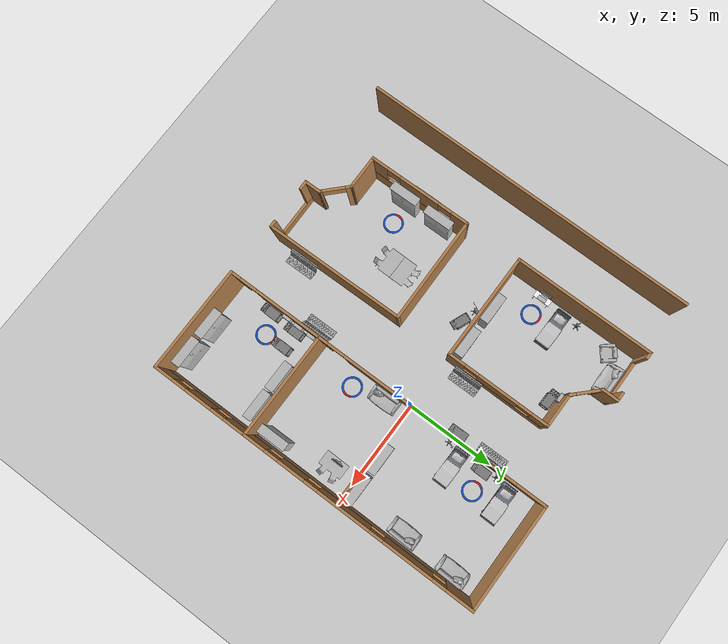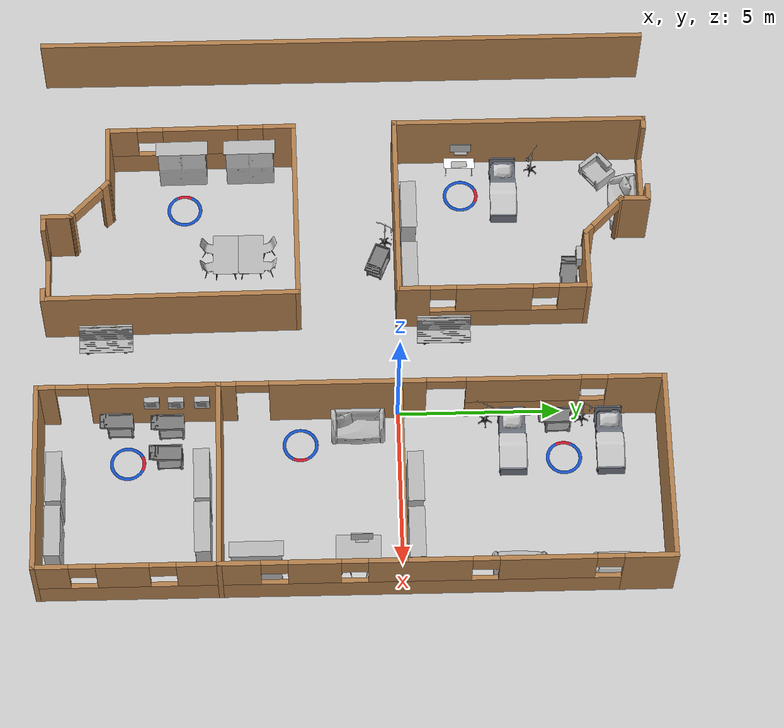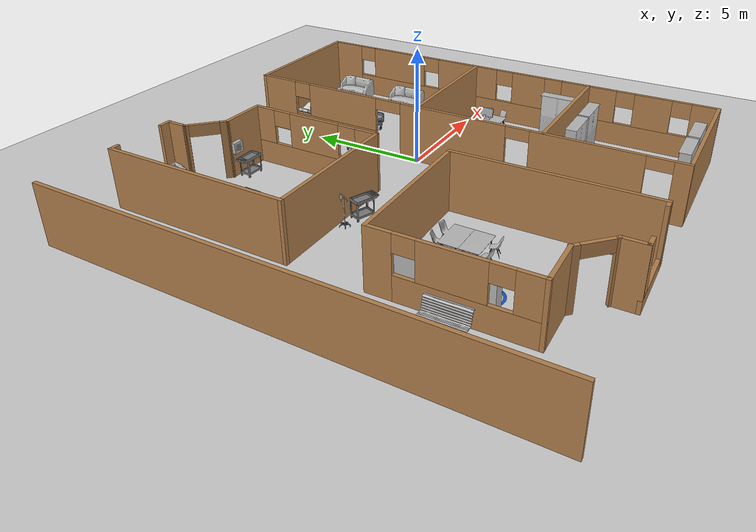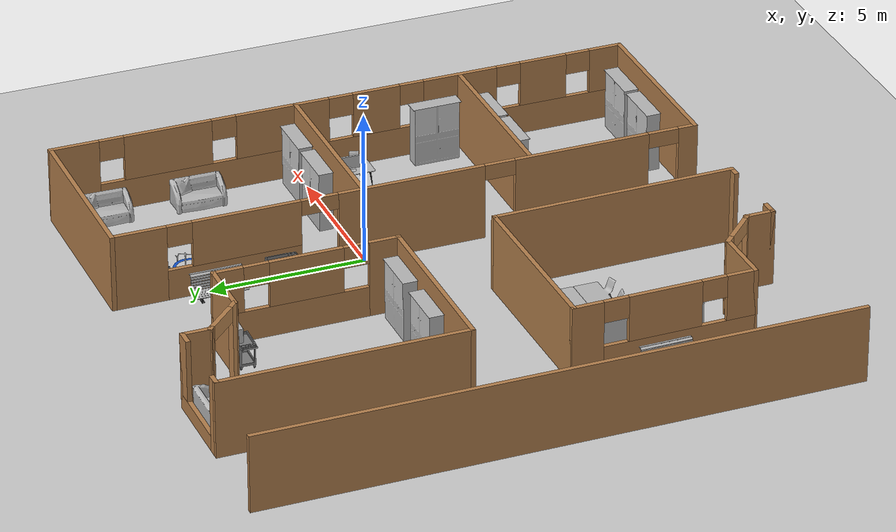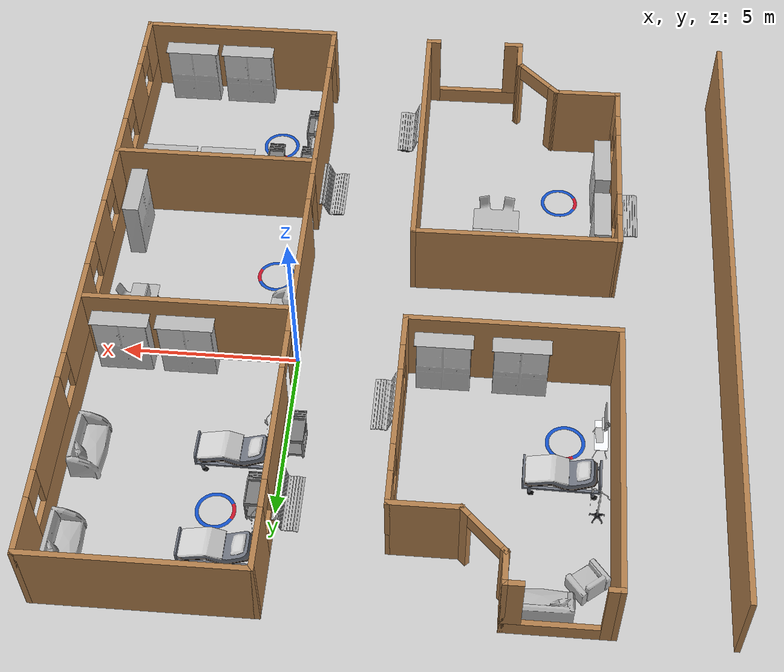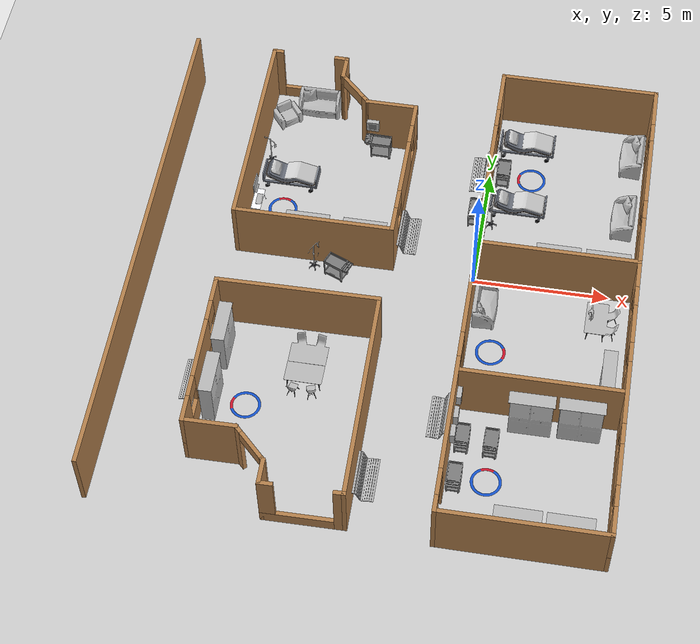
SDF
<sdf version="1.6">
 <world name="default">
  <model name="ground_plane">
   <static>1</static>
   <link name="link">
    <collision name="collision">
     <geometry><plane><normal>0 0 1</normal><size>100 100</size></plane></geometry>
     <surface>
      <contact><collide_bitmask>65535</collide_bitmask></contact>
      <friction><ode><mu>100</mu><mu2>50</mu2></ode></friction>
     </surface>
    </collision>
    <visual name="visual">
     <cast_shadows>0</cast_shadows>
     <geometry><plane><normal>0 0 1</normal><size>100 100</size></plane></geometry>
     <material>
      <script><uri>file://media/materials/scripts/gazebo.material</uri><name>Gazebo/Grey</name></script>
     </material>
    </visual>
   </link>
  </model>
  <gravity>0 0 -9.8</gravity>
  <magnetic_field>6e-06 2.3e-05 -4.2e-05</magnetic_field>
  <atmosphere type="adiabatic"/>
  <physics name="default_physics" default="0" type="ode">
   <max_step_size>0.001</max_step_size>
   <real_time_factor>1</real_time_factor>
   <real_time_update_rate>1000</real_time_update_rate>
  </physics>
  <scene><ambient>0.4 0.4 0.4 1</ambient><background>0.7 0.7 0.7 1</background><shadows>1</shadows></scene>
  <audio><device>default</device></audio>
  <spherical_coordinates>
   <surface_model>EARTH_WGS84</surface_model>
   <latitude_deg>0</latitude_deg>
   <longitude_deg>0</longitude_deg>
   <elevation>0</elevation>
   <heading_deg>0</heading_deg>
  </spherical_coordinates>
  <model name="hospital_room_empty">
   <link name="Wall_0">
    <pose>-4e-06 -3.9165 0 0 -0 0</pose>
    <visual name="Wall_0_Visual">
     <pose>0 0 1.25 0 -0 0</pose>
     <geometry><box><size>6 0.15 2.5</size></box></geometry>
     <material>
      <script><uri>file://media/materials/scripts/gazebo.material</uri><name>Gazebo/Wood</name></script>
      <ambient>1 1 1 1</ambient>
     </material>
     <meta><layer>0</layer></meta>
    </visual>
    <collision name="Wall_0_Collision">
     <pose>0 0 1.25 0 -0 0</pose>
     <geometry><box><size>6 0.15 2.5</size></box></geometry>
     <surface>
      <friction>
       <ode><mu>1</mu><mu2>1</mu2><fdir1>0 0 0</fdir1><slip1>0</slip1><slip2>0</slip2></ode>
       <torsional>
        <coefficient>1</coefficient>
        <patch_radius>0</patch_radius>
        <surface_radius>0</surface_radius>
        <use_patch_radius>1</use_patch_radius>
        <ode><slip>0</slip></ode>
       </torsional>
      </friction>
      <bounce><restitution_coefficient>0</restitution_coefficient><threshold>1e+06</threshold></bounce>
      <contact>
       <collide_without_contact>0</collide_without_contact>
       <collide_without_contact_bitmask>1</collide_without_contact_bitmask>
       <collide_bitmask>1</collide_bitmask>
       <ode>
        <soft_cfm>0</soft_cfm>
        <soft_erp>0.2</soft_erp>
        <kp>1e+13</kp>
        <kd>1</kd>
        <max_vel>0.01</max_vel>
        <min_depth>0</min_depth>
       </ode>
       <bullet>
        <split_impulse>1</split_impulse>
        <split_impulse_penetration_threshold>-0.01</split_impulse_penetration_threshold>
        <soft_cfm>0</soft_cfm>
        <soft_erp>0.2</soft_erp>
        <kp>1e+13</kp>
        <kd>1</kd>
       </bullet>
      </contact>
     </surface>
    </collision>
   </link>
   <link name="Wall_3">
    <pose>-2.925 0 0 0 -0 1.5708</pose>
    <visual name="Wall_3_Visual">
     <pose>0 0 1.25 0 -0 0</pose>
     <geometry><box><size>7.98302 0.15 2.5</size></box></geometry>
     <material>
      <script><uri>file://media/materials/scripts/gazebo.material</uri><name>Gazebo/Wood</name></script>
      <ambient>1 1 1 1</ambient>
     </material>
     <meta><layer>0</layer></meta>
    </visual>
    <collision name="Wall_3_Collision">
     <pose>0 0 1.25 0 -0 0</pose>
     <geometry><box><size>7.98302 0.15 2.5</size></box></geometry>
     <surface>
      <friction>
       <ode><mu>1</mu><mu2>1</mu2><fdir1>0 0 0</fdir1><slip1>0</slip1><slip2>0</slip2></ode>
       <torsional>
        <coefficient>1</coefficient>
        <patch_radius>0</patch_radius>
        <surface_radius>0</surface_radius>
        <use_patch_radius>1</use_patch_radius>
        <ode><slip>0</slip></ode>
       </torsional>
      </friction>
      <bounce><restitution_coefficient>0</restitution_coefficient><threshold>1e+06</threshold></bounce>
      <contact>
       <collide_without_contact>0</collide_without_contact>
       <collide_without_contact_bitmask>1</collide_without_contact_bitmask>
       <collide_bitmask>1</collide_bitmask>
       <ode>
        <soft_cfm>0</soft_cfm>
        <soft_erp>0.2</soft_erp>
        <kp>1e+13</kp>
        <kd>1</kd>
        <max_vel>0.01</max_vel>
        <min_depth>0</min_depth>
       </ode>
       <bullet>
        <split_impulse>1</split_impulse>
        <split_impulse_penetration_threshold>-0.01</split_impulse_penetration_threshold>
        <soft_cfm>0</soft_cfm>
        <soft_erp>0.2</soft_erp>
        <kp>1e+13</kp>
        <kd>1</kd>
       </bullet>
      </contact>
     </surface>
    </collision>
   </link>
   <link name="Wall_4">
    <pose>-1.5 3.9165 0 0 -0 0</pose>
    <visual name="Wall_4_Visual_0">
     <pose>-1.28125 0 1.25 0 -0 0</pose>
     <geometry><box><size>0.437506 0.15 2.5</size></box></geometry>
     <material>
      <script><uri>file://media/materials/scripts/gazebo.material</uri><name>Gazebo/Wood</name></script>
      <ambient>1 1 1 1</ambient>
     </material>
     <meta><layer>0</layer></meta>
    </visual>
    <visual name="Wall_4_Visual_1">
     <pose>0.218753 0 0.25 0 -0 0</pose>
     <geometry><box><size>2.56249 0.15 0.5</size></box></geometry>
     <material>
      <script><uri>file://media/materials/scripts/gazebo.material</uri><name>Gazebo/Wood</name></script>
      <ambient>1 1 1 1</ambient>
     </material>
     <meta><layer>0</layer></meta>
    </visual>
    <visual name="Wall_4_Visual_2">
     <pose>1.21875 0 1.5 0 -0 0</pose>
     <geometry><box><size>0.562494 0.15 2</size></box></geometry>
     <material>
      <script><uri>file://media/materials/scripts/gazebo.material</uri><name>Gazebo/Wood</name></script>
      <ambient>1 1 1 1</ambient>
     </material>
     <meta><layer>0</layer></meta>
    </visual>
    <collision name="Wall_4_Collision_0">
     <pose>-1.28125 0 1.25 0 -0 0</pose>
     <geometry><box><size>0.437506 0.15 2.5</size></box></geometry>
     <surface>
      <friction>
       <ode><mu>1</mu><mu2>1</mu2><fdir1>0 0 0</fdir1><slip1>0</slip1><slip2>0</slip2></ode>
       <torsional>
        <coefficient>1</coefficient>
        <patch_radius>0</patch_radius>
        <surface_radius>0</surface_radius>
        <use_patch_radius>1</use_patch_radius>
        <ode><slip>0</slip></ode>
       </torsional>
      </friction>
      <bounce><restitution_coefficient>0</restitution_coefficient><threshold>1e+06</threshold></bounce>
      <contact>
       <collide_without_contact>0</collide_without_contact>
       <collide_without_contact_bitmask>1</collide_without_contact_bitmask>
       <collide_bitmask>1</collide_bitmask>
       <ode>
        <soft_cfm>0</soft_cfm>
        <soft_erp>0.2</soft_erp>
        <kp>1e+13</kp>
        <kd>1</kd>
        <max_vel>0.01</max_vel>
        <min_depth>0</min_depth>
       </ode>
       <bullet>
        <split_impulse>1</split_impulse>
        <split_impulse_penetration_threshold>-0.01</split_impulse_penetration_threshold>
        <soft_cfm>0</soft_cfm>
        <soft_erp>0.2</soft_erp>
        <kp>1e+13</kp>
        <kd>1</kd>
       </bullet>
      </contact>
     </surface>
    </collision>
    <collision name="Wall_4_Collision_1">
     <pose>0.218753 0 0.25 0 -0 0</pose>
     <geometry><box><size>2.56249 0.15 0.5</size></box></geometry>
     <surface>
      <friction>
       <ode><mu>1</mu><mu2>1</mu2><fdir1>0 0 0</fdir1><slip1>0</slip1><slip2>0</slip2></ode>
       <torsional>
        <coefficient>1</coefficient>
        <patch_radius>0</patch_radius>
        <surface_radius>0</surface_radius>
        <use_patch_radius>1</use_patch_radius>
        <ode><slip>0</slip></ode>
       </torsional>
      </friction>
      <bounce><restitution_coefficient>0</restitution_coefficient><threshold>1e+06</threshold></bounce>
      <contact>
       <collide_without_contact>0</collide_without_contact>
       <collide_without_contact_bitmask>1</collide_without_contact_bitmask>
       <collide_bitmask>1</collide_bitmask>
       <ode>
        <soft_cfm>0</soft_cfm>
        <soft_erp>0.2</soft_erp>
        <kp>1e+13</kp>
        <kd>1</kd>
        <max_vel>0.01</max_vel>
        <min_depth>0</min_depth>
       </ode>
       <bullet>
        <split_impulse>1</split_impulse>
        <split_impulse_penetration_threshold>-0.01</split_impulse_penetration_threshold>
        <soft_cfm>0</soft_cfm>
        <soft_erp>0.2</soft_erp>
        <kp>1e+13</kp>
        <kd>1</kd>
       </bullet>
      </contact>
     </surface>
    </collision>
    <collision name="Wall_4_Collision_2">
     <pose>1.21875 0 1.5 0 -0 0</pose>
     <geometry><box><size>0.562494 0.15 2</size></box></geometry>
     <surface>
      <friction>
       <ode><mu>1</mu><mu2>1</mu2><fdir1>0 0 0</fdir1><slip1>0</slip1><slip2>0</slip2></ode>
       <torsional>
        <coefficient>1</coefficient>
        <patch_radius>0</patch_radius>
        <surface_radius>0</surface_radius>
        <use_patch_radius>1</use_patch_radius>
        <ode><slip>0</slip></ode>
       </torsional>
      </friction>
      <bounce><restitution_coefficient>0</restitution_coefficient><threshold>1e+06</threshold></bounce>
      <contact>
       <collide_without_contact>0</collide_without_contact>
       <collide_without_contact_bitmask>1</collide_without_contact_bitmask>
       <collide_bitmask>1</collide_bitmask>
       <ode>
        <soft_cfm>0</soft_cfm>
        <soft_erp>0.2</soft_erp>
        <kp>1e+13</kp>
        <kd>1</kd>
        <max_vel>0.01</max_vel>
        <min_depth>0</min_depth>
       </ode>
       <bullet>
        <split_impulse>1</split_impulse>
        <split_impulse_penetration_threshold>-0.01</split_impulse_penetration_threshold>
        <soft_cfm>0</soft_cfm>
        <soft_erp>0.2</soft_erp>
        <kp>1e+13</kp>
        <kd>1</kd>
       </bullet>
      </contact>
     </surface>
    </collision>
   </link>
   <link name="Wall_5">
    <pose>-0.075004 3.4915 0 0 0 -1.5708</pose>
    <visual name="Wall_5_Visual">
     <pose>0 0 1.25 0 -0 0</pose>
     <geometry><box><size>1 0.15 2.5</size></box></geometry>
     <material>
      <script><uri>file://media/materials/scripts/gazebo.material</uri><name>Gazebo/Wood</name></script>
      <ambient>1 1 1 1</ambient>
     </material>
     <meta><layer>0</layer></meta>
    </visual>
    <collision name="Wall_5_Collision">
     <pose>0 0 1.25 0 -0 0</pose>
     <geometry><box><size>1 0.15 2.5</size></box></geometry>
     <surface>
      <friction>
       <ode><mu>1</mu><mu2>1</mu2><fdir1>0 0 0</fdir1><slip1>0</slip1><slip2>0</slip2></ode>
       <torsional>
        <coefficient>1</coefficient>
        <patch_radius>0</patch_radius>
        <surface_radius>0</surface_radius>
        <use_patch_radius>1</use_patch_radius>
        <ode><slip>0</slip></ode>
       </torsional>
      </friction>
      <bounce><restitution_coefficient>0</restitution_coefficient><threshold>1e+06</threshold></bounce>
      <contact>
       <collide_without_contact>0</collide_without_contact>
       <collide_without_contact_bitmask>1</collide_without_contact_bitmask>
       <collide_bitmask>1</collide_bitmask>
       <ode>
        <soft_cfm>0</soft_cfm>
        <soft_erp>0.2</soft_erp>
        <kp>1e+13</kp>
        <kd>1</kd>
        <max_vel>0.01</max_vel>
        <min_depth>0</min_depth>
       </ode>
       <bullet>
        <split_impulse>1</split_impulse>
        <split_impulse_penetration_threshold>-0.01</split_impulse_penetration_threshold>
        <soft_cfm>0</soft_cfm>
        <soft_erp>0.2</soft_erp>
        <kp>1e+13</kp>
        <kd>1</kd>
       </bullet>
      </contact>
     </surface>
    </collision>
   </link>
   <link name="Wall_7">
    <pose>2.925 -1 0 0 -0 1.5708</pose>
    <visual name="Wall_7_Visual_0">
     <pose>-2.47597 0 1.25 0 -0 0</pose>
     <geometry><box><size>1.03106 0.15 2.5</size></box></geometry>
     <material>
      <script><uri>file://media/materials/scripts/gazebo.material</uri><name>Gazebo/Wood</name></script>
      <ambient>0.921569 0.807843 0.615686 1</ambient>
     </material>
     <meta><layer>0</layer></meta>
    </visual>
    <visual name="Wall_7_Visual_1">
     <pose>0.515531 0 0.5 0 -0 0</pose>
     <geometry><box><size>4.95194 0.15 1</size></box></geometry>
     <material>
      <script><uri>file://media/materials/scripts/gazebo.material</uri><name>Gazebo/Wood</name></script>
      <ambient>0.921569 0.807843 0.615686 1</ambient>
     </material>
     <meta><layer>0</layer></meta>
    </visual>
    <visual name="Wall_7_Visual_2">
     <pose>0.016139 0 1.75 0 -0 0</pose>
     <geometry><box><size>2.35315 0.15 1.5</size></box></geometry>
     <material>
      <script><uri>file://media/materials/scripts/gazebo.material</uri><name>Gazebo/Wood</name></script>
      <ambient>0.921569 0.807843 0.615686 1</ambient>
     </material>
     <meta><layer>0</layer></meta>
    </visual>
    <visual name="Wall_7_Visual_3">
     <pose>2.49211 0 1.75 0 -0 0</pose>
     <geometry><box><size>0.998785 0.15 1.5</size></box></geometry>
     <material>
      <script><uri>file://media/materials/scripts/gazebo.material</uri><name>Gazebo/Wood</name></script>
      <ambient>0.921569 0.807843 0.615686 1</ambient>
     </material>
     <meta><layer>0</layer></meta>
    </visual>
    <visual name="Wall_7_Visual_4">
     <pose>-1.56044 0 2.15 0 -0 0</pose>
     <geometry><box><size>0.8 0.15 0.7</size></box></geometry>
     <material>
      <script><uri>file://media/materials/scripts/gazebo.material</uri><name>Gazebo/Wood</name></script>
      <ambient>0.921569 0.807843 0.615686 1</ambient>
     </material>
     <meta><layer>0</layer></meta>
    </visual>
    <visual name="Wall_7_Visual_5">
     <pose>1.59272 0 2.15 0 -0 0</pose>
     <geometry><box><size>0.8 0.15 0.7</size></box></geometry>
     <material>
      <script><uri>file://media/materials/scripts/gazebo.material</uri><name>Gazebo/Wood</name></script>
      <ambient>0.921569 0.807843 0.615686 1</ambient>
     </material>
     <meta><layer>0</layer></meta>
    </visual>
    <collision name="Wall_7_Collision_0">
     <pose>-2.47597 0 1.25 0 -0 0</pose>
     <geometry><box><size>1.03106 0.15 2.5</size></box></geometry>
     <surface>
      <friction>
       <ode><mu>1</mu><mu2>1</mu2><fdir1>0 0 0</fdir1><slip1>0</slip1><slip2>0</slip2></ode>
       <torsional>
        <coefficient>1</coefficient>
        <patch_radius>0</patch_radius>
        <surface_radius>0</surface_radius>
        <use_patch_radius>1</use_patch_radius>
        <ode><slip>0</slip></ode>
       </torsional>
      </friction>
      <bounce><restitution_coefficient>0</restitution_coefficient><threshold>1e+06</threshold></bounce>
      <contact>
       <collide_without_contact>0</collide_without_contact>
       <collide_without_contact_bitmask>1</collide_without_contact_bitmask>
       <collide_bitmask>1</collide_bitmask>
       <ode>
        <soft_cfm>0</soft_cfm>
        <soft_erp>0.2</soft_erp>
        <kp>1e+13</kp>
        <kd>1</kd>
        <max_vel>0.01</max_vel>
        <min_depth>0</min_depth>
       </ode>
       <bullet>
        <split_impulse>1</split_impulse>
        <split_impulse_penetration_threshold>-0.01</split_impulse_penetration_threshold>
        <soft_cfm>0</soft_cfm>
        <soft_erp>0.2</soft_erp>
        <kp>1e+13</kp>
        <kd>1</kd>
       </bullet>
      </contact>
     </surface>
    </collision>
    <collision name="Wall_7_Collision_1">
     <pose>0.515531 0 0.5 0 -0 0</pose>
     <geometry><box><size>4.95194 0.15 1</size></box></geometry>
     <surface>
      <friction>
       <ode><mu>1</mu><mu2>1</mu2><fdir1>0 0 0</fdir1><slip1>0</slip1><slip2>0</slip2></ode>
       <torsional>
        <coefficient>1</coefficient>
        <patch_radius>0</patch_radius>
        <surface_radius>0</surface_radius>
        <use_patch_radius>1</use_patch_radius>
        <ode><slip>0</slip></ode>
       </torsional>
      </friction>
      <bounce><restitution_coefficient>0</restitution_coefficient><threshold>1e+06</threshold></bounce>
      <contact>
       <collide_without_contact>0</collide_without_contact>
       <collide_without_contact_bitmask>1</collide_without_contact_bitmask>
       <collide_bitmask>1</collide_bitmask>
       <ode>
        <soft_cfm>0</soft_cfm>
        <soft_erp>0.2</soft_erp>
        <kp>1e+13</kp>
        <kd>1</kd>
        <max_vel>0.01</max_vel>
        <min_depth>0</min_depth>
       </ode>
       <bullet>
        <split_impulse>1</split_impulse>
        <split_impulse_penetration_threshold>-0.01</split_impulse_penetration_threshold>
        <soft_cfm>0</soft_cfm>
        <soft_erp>0.2</soft_erp>
        <kp>1e+13</kp>
        <kd>1</kd>
       </bullet>
      </contact>
     </surface>
    </collision>
    <collision name="Wall_7_Collision_2">
     <pose>0.016139 0 1.75 0 -0 0</pose>
     <geometry><box><size>2.35315 0.15 1.5</size></box></geometry>
     <surface>
      <friction>
       <ode><mu>1</mu><mu2>1</mu2><fdir1>0 0 0</fdir1><slip1>0</slip1><slip2>0</slip2></ode>
       <torsional>
        <coefficient>1</coefficient>
        <patch_radius>0</patch_radius>
        <surface_radius>0</surface_radius>
        <use_patch_radius>1</use_patch_radius>
        <ode><slip>0</slip></ode>
       </torsional>
      </friction>
      <bounce><restitution_coefficient>0</restitution_coefficient><threshold>1e+06</threshold></bounce>
      <contact>
       <collide_without_contact>0</collide_without_contact>
       <collide_without_contact_bitmask>1</collide_without_contact_bitmask>
       <collide_bitmask>1</collide_bitmask>
       <ode>
        <soft_cfm>0</soft_cfm>
        <soft_erp>0.2</soft_erp>
        <kp>1e+13</kp>
        <kd>1</kd>
        <max_vel>0.01</max_vel>
        <min_depth>0</min_depth>
       </ode>
       <bullet>
        <split_impulse>1</split_impulse>
        <split_impulse_penetration_threshold>-0.01</split_impulse_penetration_threshold>
        <soft_cfm>0</soft_cfm>
        <soft_erp>0.2</soft_erp>
        <kp>1e+13</kp>
        <kd>1</kd>
       </bullet>
      </contact>
     </surface>
    </collision>
    <collision name="Wall_7_Collision_3">
     <pose>2.49211 0 1.75 0 -0 0</pose>
     <geometry><box><size>0.998785 0.15 1.5</size></box></geometry>
     <surface>
      <friction>
       <ode><mu>1</mu><mu2>1</mu2><fdir1>0 0 0</fdir1><slip1>0</slip1><slip2>0</slip2></ode>
       <torsional>
        <coefficient>1</coefficient>
        <patch_radius>0</patch_radius>
        <surface_radius>0</surface_radius>
        <use_patch_radius>1</use_patch_radius>
        <ode><slip>0</slip></ode>
       </torsional>
      </friction>
      <bounce><restitution_coefficient>0</restitution_coefficient><threshold>1e+06</threshold></bounce>
      <contact>
       <collide_without_contact>0</collide_without_contact>
       <collide_without_contact_bitmask>1</collide_without_contact_bitmask>
       <collide_bitmask>1</collide_bitmask>
       <ode>
        <soft_cfm>0</soft_cfm>
        <soft_erp>0.2</soft_erp>
        <kp>1e+13</kp>
        <kd>1</kd>
        <max_vel>0.01</max_vel>
        <min_depth>0</min_depth>
       </ode>
       <bullet>
        <split_impulse>1</split_impulse>
        <split_impulse_penetration_threshold>-0.01</split_impulse_penetration_threshold>
        <soft_cfm>0</soft_cfm>
        <soft_erp>0.2</soft_erp>
        <kp>1e+13</kp>
        <kd>1</kd>
       </bullet>
      </contact>
     </surface>
    </collision>
    <collision name="Wall_7_Collision_4">
     <pose>-1.56044 0 2.15 0 -0 0</pose>
     <geometry><box><size>0.8 0.15 0.7</size></box></geometry>
     <surface>
      <friction>
       <ode><mu>1</mu><mu2>1</mu2><fdir1>0 0 0</fdir1><slip1>0</slip1><slip2>0</slip2></ode>
       <torsional>
        <coefficient>1</coefficient>
        <patch_radius>0</patch_radius>
        <surface_radius>0</surface_radius>
        <use_patch_radius>1</use_patch_radius>
        <ode><slip>0</slip></ode>
       </torsional>
      </friction>
      <bounce><restitution_coefficient>0</restitution_coefficient><threshold>1e+06</threshold></bounce>
      <contact>
       <collide_without_contact>0</collide_without_contact>
       <collide_without_contact_bitmask>1</collide_without_contact_bitmask>
       <collide_bitmask>1</collide_bitmask>
       <ode>
        <soft_cfm>0</soft_cfm>
        <soft_erp>0.2</soft_erp>
        <kp>1e+13</kp>
        <kd>1</kd>
        <max_vel>0.01</max_vel>
        <min_depth>0</min_depth>
       </ode>
       <bullet>
        <split_impulse>1</split_impulse>
        <split_impulse_penetration_threshold>-0.01</split_impulse_penetration_threshold>
        <soft_cfm>0</soft_cfm>
        <soft_erp>0.2</soft_erp>
        <kp>1e+13</kp>
        <kd>1</kd>
       </bullet>
      </contact>
     </surface>
    </collision>
    <collision name="Wall_7_Collision_5">
     <pose>1.59272 0 2.15 0 -0 0</pose>
     <geometry><box><size>0.8 0.15 0.7</size></box></geometry>
     <surface>
      <friction>
       <ode><mu>1</mu><mu2>1</mu2><fdir1>0 0 0</fdir1><slip1>0</slip1><slip2>0</slip2></ode>
       <torsional>
        <coefficient>1</coefficient>
        <patch_radius>0</patch_radius>
        <surface_radius>0</surface_radius>
        <use_patch_radius>1</use_patch_radius>
        <ode><slip>0</slip></ode>
       </torsional>
      </friction>
      <bounce><restitution_coefficient>0</restitution_coefficient><threshold>1e+06</threshold></bounce>
      <contact>
       <collide_without_contact>0</collide_without_contact>
       <collide_without_contact_bitmask>1</collide_without_contact_bitmask>
       <collide_bitmask>1</collide_bitmask>
       <ode>
        <soft_cfm>0</soft_cfm>
        <soft_erp>0.2</soft_erp>
        <kp>1e+13</kp>
        <kd>1</kd>
        <max_vel>0.01</max_vel>
        <min_depth>0</min_depth>
       </ode>
       <bullet>
        <split_impulse>1</split_impulse>
        <split_impulse_penetration_threshold>-0.01</split_impulse_penetration_threshold>
        <soft_cfm>0</soft_cfm>
        <soft_erp>0.2</soft_erp>
        <kp>1e+13</kp>
        <kd>1</kd>
       </bullet>
      </contact>
     </surface>
    </collision>
   </link>
   <link name="Wall_8">
    <pose>2 1.9166 0 0 -0 3.14148</pose>
    <visual name="Wall_8_Visual">
     <pose>0 0 1.25 0 -0 0</pose>
     <geometry><box><size>2 0.15 2.5</size></box></geometry>
     <material>
      <script><uri>file://media/materials/scripts/gazebo.material</uri><name>Gazebo/Wood</name></script>
      <ambient>1 1 1 1</ambient>
     </material>
     <meta><layer>0</layer></meta>
    </visual>
    <collision name="Wall_8_Collision">
     <pose>0 0 1.25 0 -0 0</pose>
     <geometry><box><size>2 0.15 2.5</size></box></geometry>
     <surface>
      <friction>
       <ode><mu>1</mu><mu2>1</mu2><fdir1>0 0 0</fdir1><slip1>0</slip1><slip2>0</slip2></ode>
       <torsional>
        <coefficient>1</coefficient>
        <patch_radius>0</patch_radius>
        <surface_radius>0</surface_radius>
        <use_patch_radius>1</use_patch_radius>
        <ode><slip>0</slip></ode>
       </torsional>
      </friction>
      <bounce><restitution_coefficient>0</restitution_coefficient><threshold>1e+06</threshold></bounce>
      <contact>
       <collide_without_contact>0</collide_without_contact>
       <collide_without_contact_bitmask>1</collide_without_contact_bitmask>
       <collide_bitmask>1</collide_bitmask>
       <ode>
        <soft_cfm>0</soft_cfm>
        <soft_erp>0.2</soft_erp>
        <kp>1e+13</kp>
        <kd>1</kd>
        <max_vel>0.01</max_vel>
        <min_depth>0</min_depth>
       </ode>
       <bullet>
        <split_impulse>1</split_impulse>
        <split_impulse_penetration_threshold>-0.01</split_impulse_penetration_threshold>
        <soft_cfm>0</soft_cfm>
        <soft_erp>0.2</soft_erp>
        <kp>1e+13</kp>
        <kd>1</kd>
       </bullet>
      </contact>
     </surface>
    </collision>
   </link>
   <link name="Wall_9">
    <pose>0.499996 2.4916 0 0 -0 2.35628</pose>
    <visual name="Wall_9_Visual_1">
     <pose>0.785148 0 1.25 0 -0 0</pose>
     <geometry><box><size>0.205905 0.15 2.5</size></box></geometry>
     <material>
      <script><uri>file://media/materials/scripts/gazebo.material</uri><name>Gazebo/Wood</name></script>
      <ambient>1 1 1 1</ambient>
     </material>
     <meta><layer>0</layer></meta>
    </visual>
    <visual name="Wall_9_Visual_0">
     <pose>-0.702952 0 1.25 0 -0 0</pose>
     <geometry><box><size>0.370295 0.15 2.5</size></box></geometry>
     <material>
      <script><uri>file://media/materials/scripts/gazebo.material</uri><name>Gazebo/Wood</name></script>
      <ambient>1 1 1 1</ambient>
     </material>
     <meta><layer>0</layer></meta>
    </visual>
    <visual name="Wall_9_Visual_2">
     <pose>0.082195 0 2.25 0 -0 0</pose>
     <geometry><box><size>1.2 0.15 0.5</size></box></geometry>
     <material>
      <script><uri>file://media/materials/scripts/gazebo.material</uri><name>Gazebo/Wood</name></script>
      <ambient>1 1 1 1</ambient>
     </material>
     <meta><layer>0</layer></meta>
    </visual>
    <collision name="Wall_9_Collision_0">
     <pose>-0.702952 0 1.25 0 -0 0</pose>
     <geometry><box><size>0.370295 0.15 2.5</size></box></geometry>
     <surface>
      <friction>
       <ode><mu>1</mu><mu2>1</mu2><fdir1>0 0 0</fdir1><slip1>0</slip1><slip2>0</slip2></ode>
       <torsional>
        <coefficient>1</coefficient>
        <patch_radius>0</patch_radius>
        <surface_radius>0</surface_radius>
        <use_patch_radius>1</use_patch_radius>
        <ode><slip>0</slip></ode>
       </torsional>
      </friction>
      <bounce><restitution_coefficient>0</restitution_coefficient><threshold>1e+06</threshold></bounce>
      <contact>
       <collide_without_contact>0</collide_without_contact>
       <collide_without_contact_bitmask>1</collide_without_contact_bitmask>
       <collide_bitmask>1</collide_bitmask>
       <ode>
        <soft_cfm>0</soft_cfm>
        <soft_erp>0.2</soft_erp>
        <kp>1e+13</kp>
        <kd>1</kd>
        <max_vel>0.01</max_vel>
        <min_depth>0</min_depth>
       </ode>
       <bullet>
        <split_impulse>1</split_impulse>
        <split_impulse_penetration_threshold>-0.01</split_impulse_penetration_threshold>
        <soft_cfm>0</soft_cfm>
        <soft_erp>0.2</soft_erp>
        <kp>1e+13</kp>
        <kd>1</kd>
       </bullet>
      </contact>
     </surface>
    </collision>
    <collision name="Wall_9_Collision_1">
     <pose>0.785148 0 1.25 0 -0 0</pose>
     <geometry><box><size>0.205905 0.15 2.5</size></box></geometry>
     <surface>
      <friction>
       <ode><mu>1</mu><mu2>1</mu2><fdir1>0 0 0</fdir1><slip1>0</slip1><slip2>0</slip2></ode>
       <torsional>
        <coefficient>1</coefficient>
        <patch_radius>0</patch_radius>
        <surface_radius>0</surface_radius>
        <use_patch_radius>1</use_patch_radius>
        <ode><slip>0</slip></ode>
       </torsional>
      </friction>
      <bounce><restitution_coefficient>0</restitution_coefficient><threshold>1e+06</threshold></bounce>
      <contact>
       <collide_without_contact>0</collide_without_contact>
       <collide_without_contact_bitmask>1</collide_without_contact_bitmask>
       <collide_bitmask>1</collide_bitmask>
       <ode>
        <soft_cfm>0</soft_cfm>
        <soft_erp>0.2</soft_erp>
        <kp>1e+13</kp>
        <kd>1</kd>
        <max_vel>0.01</max_vel>
        <min_depth>0</min_depth>
       </ode>
       <bullet>
        <split_impulse>1</split_impulse>
        <split_impulse_penetration_threshold>-0.01</split_impulse_penetration_threshold>
        <soft_cfm>0</soft_cfm>
        <soft_erp>0.2</soft_erp>
        <kp>1e+13</kp>
        <kd>1</kd>
       </bullet>
      </contact>
     </surface>
    </collision>
    <collision name="Wall_9_Collision_2">
     <pose>0.082195 0 2.25 0 -0 0</pose>
     <geometry><box><size>1.2 0.15 0.5</size></box></geometry>
     <surface>
      <friction>
       <ode><mu>1</mu><mu2>1</mu2><fdir1>0 0 0</fdir1><slip1>0</slip1><slip2>0</slip2></ode>
       <torsional>
        <coefficient>1</coefficient>
        <patch_radius>0</patch_radius>
        <surface_radius>0</surface_radius>
        <use_patch_radius>1</use_patch_radius>
        <ode><slip>0</slip></ode>
       </torsional>
      </friction>
      <bounce><restitution_coefficient>0</restitution_coefficient><threshold>1e+06</threshold></bounce>
      <contact>
       <collide_without_contact>0</collide_without_contact>
       <collide_without_contact_bitmask>1</collide_without_contact_bitmask>
       <collide_bitmask>1</collide_bitmask>
       <ode>
        <soft_cfm>0</soft_cfm>
        <soft_erp>0.2</soft_erp>
        <kp>1e+13</kp>
        <kd>1</kd>
        <max_vel>0.01</max_vel>
        <min_depth>0</min_depth>
       </ode>
       <bullet>
        <split_impulse>1</split_impulse>
        <split_impulse_penetration_threshold>-0.01</split_impulse_penetration_threshold>
        <soft_cfm>0</soft_cfm>
        <soft_erp>0.2</soft_erp>
        <kp>1e+13</kp>
        <kd>1</kd>
       </bullet>
      </contact>
     </surface>
    </collision>
   </link>
   <static>1</static>
   <pose>-6.01115 4.00828 0 0 -0 0</pose>
  </model>
  <model name="round_sofa">
   <static>0</static>
   <link name="link">
    <inertial>
     <mass>5</mass>
     <inertia><ixx>1</ixx><ixy>0</ixy><ixz>0</ixz><iyy>1</iyy><iyz>0</iyz><izz>1</izz></inertia>
    </inertial>
    <collision name="collision">
     <geometry><mesh><uri>model://round_sofa/round_sofa.dae</uri></mesh></geometry>
    </collision>
    <visual name="visual"><geometry><mesh><uri>model://round_sofa/round_sofa.dae</uri></mesh></geometry></visual>
   </link>
   <pose>-6.98546 7.36312 0.005557 -0.003617 -0.001768 -2.2e-05</pose>
  </model>
  <model name="single_sofa">
   <static>0</static>
   <link name="link">
    <inertial>
     <mass>10</mass>
     <inertia><ixx>1</ixx><ixy>0</ixy><ixz>0</ixz><iyy>1</iyy><iyz>0</iyz><izz>1</izz></inertia>
    </inertial>
    <collision name="collision">
     <geometry><mesh><uri>model://single_sofa/single_sofa.dae</uri></mesh></geometry>
    </collision>
    <visual name="visual">
     <geometry><mesh><uri>model://single_sofa/single_sofa.dae</uri></mesh></geometry>
    </visual>
   </link>
   <pose>-8.19763 6.51732 -0.002743 0.000566 -8e-06 0.673255</pose>
  </model>
  <model name="iv_pole">
   <static>0</static>
   <link name="link">
    <inertial>
     <mass>5</mass>
     <inertia><ixx>1</ixx><ixy>0</ixy><ixz>0</ixz><iyy>1</iyy><iyz>0</iyz><izz>1</izz></inertia>
    </inertial>
    <collision name="collision">
     <geometry><mesh><uri>model://iv_pole/iv_pole.dae</uri></mesh></geometry>
    </collision>
    <visual name="visual"><geometry><mesh><uri>model://iv_pole/iv_pole.dae</uri></mesh></geometry></visual>
   </link>
   <pose>-8.42965 4.47468 0.012685 0.005084 -0.008775 -1.61481</pose>
  </model>
  <model name="service_cart">
   <static>0</static>
   <link name="link">
    <inertial>
     <mass>10</mass>
     <inertia><ixx>1</ixx><ixy>0</ixy><ixz>0</ixz><iyy>1</iyy><iyz>0</iyz><izz>1</izz></inertia>
    </inertial>
    <collision name="collision">
     <geometry><mesh><uri>model://service_cart/service_cart.dae</uri></mesh></geometry>
    </collision>
    <visual name="visual">
     <geometry><mesh><uri>model://service_cart/service_cart.dae</uri></mesh></geometry>
    </visual>
   </link>
   <pose>-4.43393 5.44631 -0.000537 0.001184 0.000487 -1.59205</pose>
  </model>
  <model name="wall_locker">
   <static>1</static>
   <link name="link">
    <inertial>
     <mass>10</mass>
     <inertia><ixx>1</ixx><ixy>0</ixy><ixz>0</ixz><iyy>1</iyy><iyz>0</iyz><izz>1</izz></inertia>
    </inertial>
    <collision name="collision">
     <geometry><mesh><uri>model://wall_locker/wall_locker.dae</uri></mesh></geometry>
    </collision>
    <visual name="visual">
     <geometry><mesh><uri>model://wall_locker/wall_locker.dae</uri></mesh></geometry>
    </visual>
   </link>
   <pose>-4.74054 5.91223 0.876651 0 0 -1.59389</pose>
  </model>
  <model name="travel_bag">
   <static>0</static>
   <link name="link">
    <inertial>
     <mass>20</mass>
     <inertia><ixx>1</ixx><ixy>0</ixy><ixz>0</ixz><iyy>1</iyy><iyz>0</iyz><izz>1</izz></inertia>
    </inertial>
    <collision name="collision">
     <geometry><mesh><uri>model://hospital_bed/hospital_bed.dae</uri></mesh></geometry>
    </collision>
    <visual name="visual">
     <geometry><mesh><uri>model://hospital_bed/hospital_bed.dae</uri></mesh></geometry>
    </visual>
   </link>
   <pose>-7.51874 3.53795 -0.001742 0 0.000955 3.12824</pose>
  </model>
  <model name="ikea_desk">
   <static>0</static>
   <link name="link">
    <inertial>
     <mass>5</mass>
     <inertia><ixx>1</ixx><ixy>0</ixy><ixz>0</ixz><iyy>1</iyy><iyz>0</iyz><izz>1</izz></inertia>
    </inertial>
    <collision name="collision">
     <geometry><mesh><uri>model://ikea_desk/ikea_desk.dae</uri></mesh></geometry>
    </collision>
    <visual name="visual"><geometry><mesh><uri>model://ikea_desk/ikea_desk.dae</uri></mesh></geometry></visual>
   </link>
   <pose>-8.55722 2.15414 0.029123 2.1e-05 7.6e-05 -0.017243</pose>
  </model>
  <model name="keyboard">
   <static>0</static>
   <link name="link">
    <inertial>
     <mass>5</mass>
     <inertia><ixx>1</ixx><ixy>0</ixy><ixz>0</ixz><iyy>1</iyy><iyz>0</iyz><izz>1</izz></inertia>
    </inertial>
    <collision name="collision">
     <geometry><mesh><uri>model://keyboard/keyboard.dae</uri></mesh></geometry>
    </collision>
    <visual name="visual"><geometry><mesh><uri>model://keyboard/keyboard.dae</uri></mesh></geometry></visual>
   </link>
   <pose>-8.50759 2.17811 0.480699 0.001287 -0.000241 1.57377</pose>
  </model>
  <model name="computer_monitor">
   <static>1</static>
   <link name="link">
    <inertial>
     <mass>1</mass>
     <inertia><ixx>0.05</ixx><ixy>0</ixy><ixz>0</ixz><iyy>0.05</iyy><iyz>0</iyz><izz>0.05</izz></inertia>
    </inertial>
    <collision name="collision">
     <geometry><mesh><uri>model://computer_monitor/computer_monitor.dae</uri></mesh></geometry>
    </collision>
    <visual name="visual">
     <geometry><mesh><uri>model://computer_monitor/computer_monitor.dae</uri></mesh></geometry>
    </visual>
   </link>
   <pose>-8.59142 2.20193 1.07378 0 -0 1.55927</pose>
  </model>
  <model name="closet_0">
   <static>0</static>
   <link name="link">
    <inertial>
     <mass>10</mass>
     <inertia><ixx>0.2</ixx><ixy>0</ixy><ixz>0</ixz><iyy>0.2</iyy><iyz>0</iyz><izz>0.2</izz></inertia>
    </inertial>
    <collision name="collision"><geometry><mesh><uri>model://closet/closet.dae</uri></mesh></geometry></collision>
    <visual name="visual"><geometry><mesh><uri>model://closet/closet.dae</uri></mesh></geometry></visual>
   </link>
   <pose>-4.15936 0.43493 -0.03 0 -0 0.000221</pose>
  </model>
  <model name="closet_1">
   <static>0</static>
   <link name="link">
    <inertial>
     <mass>10</mass>
     <inertia><ixx>0.2</ixx><ixy>0</ixy><ixz>0</ixz><iyy>0.2</iyy><iyz>0</iyz><izz>0.2</izz></inertia>
    </inertial>
    <collision name="collision"><geometry><mesh><uri>model://closet/closet.dae</uri></mesh></geometry></collision>
    <visual name="visual"><geometry><mesh><uri>model://closet/closet.dae</uri></mesh></geometry></visual>
   </link>
   <pose>-6.29052 0.454272 -0.03 0 -0 0.000221</pose>
  </model>
  <model name="hospital_room_empty_clone">
   <link name="Wall_0">
    <pose>-4e-06 -3.9165 0 0 -0 0</pose>
    <visual name="Wall_0_Visual">
     <pose>0 0 1.25 0 -0 0</pose>
     <geometry><box><size>6 0.15 2.5</size></box></geometry>
     <material>
      <script><uri>file://media/materials/scripts/gazebo.material</uri><name>Gazebo/Wood</name></script>
      <ambient>1 1 1 1</ambient>
     </material>
     <meta><layer>0</layer></meta>
    </visual>
    <collision name="Wall_0_Collision">
     <pose>0 0 1.25 0 -0 0</pose>
     <geometry><box><size>6 0.15 2.5</size></box></geometry>
     <surface>
      <friction>
       <ode><mu>1</mu><mu2>1</mu2><fdir1>0 0 0</fdir1><slip1>0</slip1><slip2>0</slip2></ode>
       <torsional>
        <coefficient>1</coefficient>
        <patch_radius>0</patch_radius>
        <surface_radius>0</surface_radius>
        <use_patch_radius>1</use_patch_radius>
        <ode><slip>0</slip></ode>
       </torsional>
      </friction>
      <bounce><restitution_coefficient>0</restitution_coefficient><threshold>1e+06</threshold></bounce>
      <contact>
       <collide_without_contact>0</collide_without_contact>
       <collide_without_contact_bitmask>1</collide_without_contact_bitmask>
       <collide_bitmask>1</collide_bitmask>
       <ode>
        <soft_cfm>0</soft_cfm>
        <soft_erp>0.2</soft_erp>
        <kp>1e+13</kp>
        <kd>1</kd>
        <max_vel>0.01</max_vel>
        <min_depth>0</min_depth>
       </ode>
       <bullet>
        <split_impulse>1</split_impulse>
        <split_impulse_penetration_threshold>-0.01</split_impulse_penetration_threshold>
        <soft_cfm>0</soft_cfm>
        <soft_erp>0.2</soft_erp>
        <kp>1e+13</kp>
        <kd>1</kd>
       </bullet>
      </contact>
     </surface>
    </collision>
   </link>
   <link name="Wall_3">
    <pose>-2.925 0 0 0 -0 1.5708</pose>
    <visual name="Wall_3_Visual">
     <pose>0 0 1.25 0 -0 0</pose>
     <geometry><box><size>7.98302 0.15 2.5</size></box></geometry>
     <material>
      <script><uri>file://media/materials/scripts/gazebo.material</uri><name>Gazebo/Wood</name></script>
      <ambient>1 1 1 1</ambient>
     </material>
     <meta><layer>0</layer></meta>
    </visual>
    <collision name="Wall_3_Collision">
     <pose>0 0 1.25 0 -0 0</pose>
     <geometry><box><size>7.98302 0.15 2.5</size></box></geometry>
     <surface>
      <friction>
       <ode><mu>1</mu><mu2>1</mu2><fdir1>0 0 0</fdir1><slip1>0</slip1><slip2>0</slip2></ode>
       <torsional>
        <coefficient>1</coefficient>
        <patch_radius>0</patch_radius>
        <surface_radius>0</surface_radius>
        <use_patch_radius>1</use_patch_radius>
        <ode><slip>0</slip></ode>
       </torsional>
      </friction>
      <bounce><restitution_coefficient>0</restitution_coefficient><threshold>1e+06</threshold></bounce>
      <contact>
       <collide_without_contact>0</collide_without_contact>
       <collide_without_contact_bitmask>1</collide_without_contact_bitmask>
       <collide_bitmask>1</collide_bitmask>
       <ode>
        <soft_cfm>0</soft_cfm>
        <soft_erp>0.2</soft_erp>
        <kp>1e+13</kp>
        <kd>1</kd>
        <max_vel>0.01</max_vel>
        <min_depth>0</min_depth>
       </ode>
       <bullet>
        <split_impulse>1</split_impulse>
        <split_impulse_penetration_threshold>-0.01</split_impulse_penetration_threshold>
        <soft_cfm>0</soft_cfm>
        <soft_erp>0.2</soft_erp>
        <kp>1e+13</kp>
        <kd>1</kd>
       </bullet>
      </contact>
     </surface>
    </collision>
   </link>
   <link name="Wall_4">
    <pose>-1.5 3.9165 0 0 -0 0</pose>
    <visual name="Wall_4_Visual_0">
     <pose>-1.28125 0 1.25 0 -0 0</pose>
     <geometry><box><size>0.437506 0.15 2.5</size></box></geometry>
     <material>
      <script><uri>file://media/materials/scripts/gazebo.material</uri><name>Gazebo/Wood</name></script>
      <ambient>1 1 1 1</ambient>
     </material>
     <meta><layer>0</layer></meta>
    </visual>
    <visual name="Wall_4_Visual_1">
     <pose>0.218753 0 0.25 0 -0 0</pose>
     <geometry><box><size>2.56249 0.15 0.5</size></box></geometry>
     <material>
      <script><uri>file://media/materials/scripts/gazebo.material</uri><name>Gazebo/Wood</name></script>
      <ambient>1 1 1 1</ambient>
     </material>
     <meta><layer>0</layer></meta>
    </visual>
    <visual name="Wall_4_Visual_2">
     <pose>1.21875 0 1.5 0 -0 0</pose>
     <geometry><box><size>0.562494 0.15 2</size></box></geometry>
     <material>
      <script><uri>file://media/materials/scripts/gazebo.material</uri><name>Gazebo/Wood</name></script>
      <ambient>1 1 1 1</ambient>
     </material>
     <meta><layer>0</layer></meta>
    </visual>
    <collision name="Wall_4_Collision_0">
     <pose>-1.28125 0 1.25 0 -0 0</pose>
     <geometry><box><size>0.437506 0.15 2.5</size></box></geometry>
     <surface>
      <friction>
       <ode><mu>1</mu><mu2>1</mu2><fdir1>0 0 0</fdir1><slip1>0</slip1><slip2>0</slip2></ode>
       <torsional>
        <coefficient>1</coefficient>
        <patch_radius>0</patch_radius>
        <surface_radius>0</surface_radius>
        <use_patch_radius>1</use_patch_radius>
        <ode><slip>0</slip></ode>
       </torsional>
      </friction>
      <bounce><restitution_coefficient>0</restitution_coefficient><threshold>1e+06</threshold></bounce>
      <contact>
       <collide_without_contact>0</collide_without_contact>
       <collide_without_contact_bitmask>1</collide_without_contact_bitmask>
       <collide_bitmask>1</collide_bitmask>
       <ode>
        <soft_cfm>0</soft_cfm>
        <soft_erp>0.2</soft_erp>
        <kp>1e+13</kp>
        <kd>1</kd>
        <max_vel>0.01</max_vel>
        <min_depth>0</min_depth>
       </ode>
       <bullet>
        <split_impulse>1</split_impulse>
        <split_impulse_penetration_threshold>-0.01</split_impulse_penetration_threshold>
        <soft_cfm>0</soft_cfm>
        <soft_erp>0.2</soft_erp>
        <kp>1e+13</kp>
        <kd>1</kd>
       </bullet>
      </contact>
     </surface>
    </collision>
    <collision name="Wall_4_Collision_1">
     <pose>0.218753 0 0.25 0 -0 0</pose>
     <geometry><box><size>2.56249 0.15 0.5</size></box></geometry>
     <surface>
      <friction>
       <ode><mu>1</mu><mu2>1</mu2><fdir1>0 0 0</fdir1><slip1>0</slip1><slip2>0</slip2></ode>
       <torsional>
        <coefficient>1</coefficient>
        <patch_radius>0</patch_radius>
        <surface_radius>0</surface_radius>
        <use_patch_radius>1</use_patch_radius>
        <ode><slip>0</slip></ode>
       </torsional>
      </friction>
      <bounce><restitution_coefficient>0</restitution_coefficient><threshold>1e+06</threshold></bounce>
      <contact>
       <collide_without_contact>0</collide_without_contact>
       <collide_without_contact_bitmask>1</collide_without_contact_bitmask>
       <collide_bitmask>1</collide_bitmask>
       <ode>
        <soft_cfm>0</soft_cfm>
        <soft_erp>0.2</soft_erp>
        <kp>1e+13</kp>
        <kd>1</kd>
        <max_vel>0.01</max_vel>
        <min_depth>0</min_depth>
       </ode>
       <bullet>
        <split_impulse>1</split_impulse>
        <split_impulse_penetration_threshold>-0.01</split_impulse_penetration_threshold>
        <soft_cfm>0</soft_cfm>
        <soft_erp>0.2</soft_erp>
        <kp>1e+13</kp>
        <kd>1</kd>
       </bullet>
      </contact>
     </surface>
    </collision>
    <collision name="Wall_4_Collision_2">
     <pose>1.21875 0 1.5 0 -0 0</pose>
     <geometry><box><size>0.562494 0.15 2</size></box></geometry>
     <surface>
      <friction>
       <ode><mu>1</mu><mu2>1</mu2><fdir1>0 0 0</fdir1><slip1>0</slip1><slip2>0</slip2></ode>
       <torsional>
        <coefficient>1</coefficient>
        <patch_radius>0</patch_radius>
        <surface_radius>0</surface_radius>
        <use_patch_radius>1</use_patch_radius>
        <ode><slip>0</slip></ode>
       </torsional>
      </friction>
      <bounce><restitution_coefficient>0</restitution_coefficient><threshold>1e+06</threshold></bounce>
      <contact>
       <collide_without_contact>0</collide_without_contact>
       <collide_without_contact_bitmask>1</collide_without_contact_bitmask>
       <collide_bitmask>1</collide_bitmask>
       <ode>
        <soft_cfm>0</soft_cfm>
        <soft_erp>0.2</soft_erp>
        <kp>1e+13</kp>
        <kd>1</kd>
        <max_vel>0.01</max_vel>
        <min_depth>0</min_depth>
       </ode>
       <bullet>
        <split_impulse>1</split_impulse>
        <split_impulse_penetration_threshold>-0.01</split_impulse_penetration_threshold>
        <soft_cfm>0</soft_cfm>
        <soft_erp>0.2</soft_erp>
        <kp>1e+13</kp>
        <kd>1</kd>
       </bullet>
      </contact>
     </surface>
    </collision>
   </link>
   <link name="Wall_5">
    <pose>-0.075004 3.4915 0 0 0 -1.5708</pose>
    <visual name="Wall_5_Visual">
     <pose>0 0 1.25 0 -0 0</pose>
     <geometry><box><size>1 0.15 2.5</size></box></geometry>
     <material>
      <script><uri>file://media/materials/scripts/gazebo.material</uri><name>Gazebo/Wood</name></script>
      <ambient>1 1 1 1</ambient>
     </material>
     <meta><layer>0</layer></meta>
    </visual>
    <collision name="Wall_5_Collision">
     <pose>0 0 1.25 0 -0 0</pose>
     <geometry><box><size>1 0.15 2.5</size></box></geometry>
     <surface>
      <friction>
       <ode><mu>1</mu><mu2>1</mu2><fdir1>0 0 0</fdir1><slip1>0</slip1><slip2>0</slip2></ode>
       <torsional>
        <coefficient>1</coefficient>
        <patch_radius>0</patch_radius>
        <surface_radius>0</surface_radius>
        <use_patch_radius>1</use_patch_radius>
        <ode><slip>0</slip></ode>
       </torsional>
      </friction>
      <bounce><restitution_coefficient>0</restitution_coefficient><threshold>1e+06</threshold></bounce>
      <contact>
       <collide_without_contact>0</collide_without_contact>
       <collide_without_contact_bitmask>1</collide_without_contact_bitmask>
       <collide_bitmask>1</collide_bitmask>
       <ode>
        <soft_cfm>0</soft_cfm>
        <soft_erp>0.2</soft_erp>
        <kp>1e+13</kp>
        <kd>1</kd>
        <max_vel>0.01</max_vel>
        <min_depth>0</min_depth>
       </ode>
       <bullet>
        <split_impulse>1</split_impulse>
        <split_impulse_penetration_threshold>-0.01</split_impulse_penetration_threshold>
        <soft_cfm>0</soft_cfm>
        <soft_erp>0.2</soft_erp>
        <kp>1e+13</kp>
        <kd>1</kd>
       </bullet>
      </contact>
     </surface>
    </collision>
   </link>
   <link name="Wall_7">
    <pose>2.925 -1 0 0 -0 1.5708</pose>
    <visual name="Wall_7_Visual_0">
     <pose>-2.47597 0 1.25 0 -0 0</pose>
     <geometry><box><size>1.03106 0.15 2.5</size></box></geometry>
     <material>
      <script><uri>file://media/materials/scripts/gazebo.material</uri><name>Gazebo/Wood</name></script>
      <ambient>0.921569 0.807843 0.615686 1</ambient>
     </material>
     <meta><layer>0</layer></meta>
    </visual>
    <visual name="Wall_7_Visual_1">
     <pose>0.515531 0 0.5 0 -0 0</pose>
     <geometry><box><size>4.95194 0.15 1</size></box></geometry>
     <material>
      <script><uri>file://media/materials/scripts/gazebo.material</uri><name>Gazebo/Wood</name></script>
      <ambient>0.921569 0.807843 0.615686 1</ambient>
     </material>
     <meta><layer>0</layer></meta>
    </visual>
    <visual name="Wall_7_Visual_2">
     <pose>0.016139 0 1.75 0 -0 0</pose>
     <geometry><box><size>2.35315 0.15 1.5</size></box></geometry>
     <material>
      <script><uri>file://media/materials/scripts/gazebo.material</uri><name>Gazebo/Wood</name></script>
      <ambient>0.921569 0.807843 0.615686 1</ambient>
     </material>
     <meta><layer>0</layer></meta>
    </visual>
    <visual name="Wall_7_Visual_3">
     <pose>2.49211 0 1.75 0 -0 0</pose>
     <geometry><box><size>0.998785 0.15 1.5</size></box></geometry>
     <material>
      <script><uri>file://media/materials/scripts/gazebo.material</uri><name>Gazebo/Wood</name></script>
      <ambient>0.921569 0.807843 0.615686 1</ambient>
     </material>
     <meta><layer>0</layer></meta>
    </visual>
    <visual name="Wall_7_Visual_4">
     <pose>-1.56044 0 2.15 0 -0 0</pose>
     <geometry><box><size>0.8 0.15 0.7</size></box></geometry>
     <material>
      <script><uri>file://media/materials/scripts/gazebo.material</uri><name>Gazebo/Wood</name></script>
      <ambient>0.921569 0.807843 0.615686 1</ambient>
     </material>
     <meta><layer>0</layer></meta>
    </visual>
    <visual name="Wall_7_Visual_5">
     <pose>1.59272 0 2.15 0 -0 0</pose>
     <geometry><box><size>0.8 0.15 0.7</size></box></geometry>
     <material>
      <script><uri>file://media/materials/scripts/gazebo.material</uri><name>Gazebo/Wood</name></script>
      <ambient>0.921569 0.807843 0.615686 1</ambient>
     </material>
     <meta><layer>0</layer></meta>
    </visual>
    <collision name="Wall_7_Collision_0">
     <pose>-2.47597 0 1.25 0 -0 0</pose>
     <geometry><box><size>1.03106 0.15 2.5</size></box></geometry>
     <surface>
      <friction>
       <ode><mu>1</mu><mu2>1</mu2><fdir1>0 0 0</fdir1><slip1>0</slip1><slip2>0</slip2></ode>
       <torsional>
        <coefficient>1</coefficient>
        <patch_radius>0</patch_radius>
        <surface_radius>0</surface_radius>
        <use_patch_radius>1</use_patch_radius>
        <ode><slip>0</slip></ode>
       </torsional>
      </friction>
      <bounce><restitution_coefficient>0</restitution_coefficient><threshold>1e+06</threshold></bounce>
      <contact>
       <collide_without_contact>0</collide_without_contact>
       <collide_without_contact_bitmask>1</collide_without_contact_bitmask>
       <collide_bitmask>1</collide_bitmask>
       <ode>
        <soft_cfm>0</soft_cfm>
        <soft_erp>0.2</soft_erp>
        <kp>1e+13</kp>
        <kd>1</kd>
        <max_vel>0.01</max_vel>
        <min_depth>0</min_depth>
       </ode>
       <bullet>
        <split_impulse>1</split_impulse>
        <split_impulse_penetration_threshold>-0.01</split_impulse_penetration_threshold>
        <soft_cfm>0</soft_cfm>
        <soft_erp>0.2</soft_erp>
        <kp>1e+13</kp>
        <kd>1</kd>
       </bullet>
      </contact>
     </surface>
    </collision>
    <collision name="Wall_7_Collision_1">
     <pose>0.515531 0 0.5 0 -0 0</pose>
     <geometry><box><size>4.95194 0.15 1</size></box></geometry>
     <surface>
      <friction>
       <ode><mu>1</mu><mu2>1</mu2><fdir1>0 0 0</fdir1><slip1>0</slip1><slip2>0</slip2></ode>
       <torsional>
        <coefficient>1</coefficient>
        <patch_radius>0</patch_radius>
        <surface_radius>0</surface_radius>
        <use_patch_radius>1</use_patch_radius>
        <ode><slip>0</slip></ode>
       </torsional>
      </friction>
      <bounce><restitution_coefficient>0</restitution_coefficient><threshold>1e+06</threshold></bounce>
      <contact>
       <collide_without_contact>0</collide_without_contact>
       <collide_without_contact_bitmask>1</collide_without_contact_bitmask>
       <collide_bitmask>1</collide_bitmask>
       <ode>
        <soft_cfm>0</soft_cfm>
        <soft_erp>0.2</soft_erp>
        <kp>1e+13</kp>
        <kd>1</kd>
        <max_vel>0.01</max_vel>
        <min_depth>0</min_depth>
       </ode>
       <bullet>
        <split_impulse>1</split_impulse>
        <split_impulse_penetration_threshold>-0.01</split_impulse_penetration_threshold>
        <soft_cfm>0</soft_cfm>
        <soft_erp>0.2</soft_erp>
        <kp>1e+13</kp>
        <kd>1</kd>
       </bullet>
      </contact>
     </surface>
    </collision>
    <collision name="Wall_7_Collision_2">
     <pose>0.016139 0 1.75 0 -0 0</pose>
     <geometry><box><size>2.35315 0.15 1.5</size></box></geometry>
     <surface>
      <friction>
       <ode><mu>1</mu><mu2>1</mu2><fdir1>0 0 0</fdir1><slip1>0</slip1><slip2>0</slip2></ode>
       <torsional>
        <coefficient>1</coefficient>
        <patch_radius>0</patch_radius>
        <surface_radius>0</surface_radius>
        <use_patch_radius>1</use_patch_radius>
        <ode><slip>0</slip></ode>
       </torsional>
      </friction>
      <bounce><restitution_coefficient>0</restitution_coefficient><threshold>1e+06</threshold></bounce>
      <contact>
       <collide_without_contact>0</collide_without_contact>
       <collide_without_contact_bitmask>1</collide_without_contact_bitmask>
       <collide_bitmask>1</collide_bitmask>
       <ode>
        <soft_cfm>0</soft_cfm>
        <soft_erp>0.2</soft_erp>
        <kp>1e+13</kp>
        <kd>1</kd>
        <max_vel>0.01</max_vel>
        <min_depth>0</min_depth>
       </ode>
       <bullet>
        <split_impulse>1</split_impulse>
        <split_impulse_penetration_threshold>-0.01</split_impulse_penetration_threshold>
        <soft_cfm>0</soft_cfm>
        <soft_erp>0.2</soft_erp>
        <kp>1e+13</kp>
        <kd>1</kd>
       </bullet>
      </contact>
     </surface>
    </collision>
    <collision name="Wall_7_Collision_3">
     <pose>2.49211 0 1.75 0 -0 0</pose>
     <geometry><box><size>0.998785 0.15 1.5</size></box></geometry>
     <surface>
      <friction>
       <ode><mu>1</mu><mu2>1</mu2><fdir1>0 0 0</fdir1><slip1>0</slip1><slip2>0</slip2></ode>
       <torsional>
        <coefficient>1</coefficient>
        <patch_radius>0</patch_radius>
        <surface_radius>0</surface_radius>
        <use_patch_radius>1</use_patch_radius>
        <ode><slip>0</slip></ode>
       </torsional>
      </friction>
      <bounce><restitution_coefficient>0</restitution_coefficient><threshold>1e+06</threshold></bounce>
      <contact>
       <collide_without_contact>0</collide_without_contact>
       <collide_without_contact_bitmask>1</collide_without_contact_bitmask>
       <collide_bitmask>1</collide_bitmask>
       <ode>
        <soft_cfm>0</soft_cfm>
        <soft_erp>0.2</soft_erp>
        <kp>1e+13</kp>
        <kd>1</kd>
        <max_vel>0.01</max_vel>
        <min_depth>0</min_depth>
       </ode>
       <bullet>
        <split_impulse>1</split_impulse>
        <split_impulse_penetration_threshold>-0.01</split_impulse_penetration_threshold>
        <soft_cfm>0</soft_cfm>
        <soft_erp>0.2</soft_erp>
        <kp>1e+13</kp>
        <kd>1</kd>
       </bullet>
      </contact>
     </surface>
    </collision>
    <collision name="Wall_7_Collision_4">
     <pose>-1.56044 0 2.15 0 -0 0</pose>
     <geometry><box><size>0.8 0.15 0.7</size></box></geometry>
     <surface>
      <friction>
       <ode><mu>1</mu><mu2>1</mu2><fdir1>0 0 0</fdir1><slip1>0</slip1><slip2>0</slip2></ode>
       <torsional>
        <coefficient>1</coefficient>
        <patch_radius>0</patch_radius>
        <surface_radius>0</surface_radius>
        <use_patch_radius>1</use_patch_radius>
        <ode><slip>0</slip></ode>
       </torsional>
      </friction>
      <bounce><restitution_coefficient>0</restitution_coefficient><threshold>1e+06</threshold></bounce>
      <contact>
       <collide_without_contact>0</collide_without_contact>
       <collide_without_contact_bitmask>1</collide_without_contact_bitmask>
       <collide_bitmask>1</collide_bitmask>
       <ode>
        <soft_cfm>0</soft_cfm>
        <soft_erp>0.2</soft_erp>
        <kp>1e+13</kp>
        <kd>1</kd>
        <max_vel>0.01</max_vel>
        <min_depth>0</min_depth>
       </ode>
       <bullet>
        <split_impulse>1</split_impulse>
        <split_impulse_penetration_threshold>-0.01</split_impulse_penetration_threshold>
        <soft_cfm>0</soft_cfm>
        <soft_erp>0.2</soft_erp>
        <kp>1e+13</kp>
        <kd>1</kd>
       </bullet>
      </contact>
     </surface>
    </collision>
    <collision name="Wall_7_Collision_5">
     <pose>1.59272 0 2.15 0 -0 0</pose>
     <geometry><box><size>0.8 0.15 0.7</size></box></geometry>
     <surface>
      <friction>
       <ode><mu>1</mu><mu2>1</mu2><fdir1>0 0 0</fdir1><slip1>0</slip1><slip2>0</slip2></ode>
       <torsional>
        <coefficient>1</coefficient>
        <patch_radius>0</patch_radius>
        <surface_radius>0</surface_radius>
        <use_patch_radius>1</use_patch_radius>
        <ode><slip>0</slip></ode>
       </torsional>
      </friction>
      <bounce><restitution_coefficient>0</restitution_coefficient><threshold>1e+06</threshold></bounce>
      <contact>
       <collide_without_contact>0</collide_without_contact>
       <collide_without_contact_bitmask>1</collide_without_contact_bitmask>
       <collide_bitmask>1</collide_bitmask>
       <ode>
        <soft_cfm>0</soft_cfm>
        <soft_erp>0.2</soft_erp>
        <kp>1e+13</kp>
        <kd>1</kd>
        <max_vel>0.01</max_vel>
        <min_depth>0</min_depth>
       </ode>
       <bullet>
        <split_impulse>1</split_impulse>
        <split_impulse_penetration_threshold>-0.01</split_impulse_penetration_threshold>
        <soft_cfm>0</soft_cfm>
        <soft_erp>0.2</soft_erp>
        <kp>1e+13</kp>
        <kd>1</kd>
       </bullet>
      </contact>
     </surface>
    </collision>
   </link>
   <link name="Wall_8">
    <pose>2 1.9166 0 0 -0 3.14148</pose>
    <visual name="Wall_8_Visual">
     <pose>0 0 1.25 0 -0 0</pose>
     <geometry><box><size>2 0.15 2.5</size></box></geometry>
     <material>
      <script><uri>file://media/materials/scripts/gazebo.material</uri><name>Gazebo/Wood</name></script>
      <ambient>1 1 1 1</ambient>
     </material>
     <meta><layer>0</layer></meta>
    </visual>
    <collision name="Wall_8_Collision">
     <pose>0 0 1.25 0 -0 0</pose>
     <geometry><box><size>2 0.15 2.5</size></box></geometry>
     <surface>
      <friction>
       <ode><mu>1</mu><mu2>1</mu2><fdir1>0 0 0</fdir1><slip1>0</slip1><slip2>0</slip2></ode>
       <torsional>
        <coefficient>1</coefficient>
        <patch_radius>0</patch_radius>
        <surface_radius>0</surface_radius>
        <use_patch_radius>1</use_patch_radius>
        <ode><slip>0</slip></ode>
       </torsional>
      </friction>
      <bounce><restitution_coefficient>0</restitution_coefficient><threshold>1e+06</threshold></bounce>
      <contact>
       <collide_without_contact>0</collide_without_contact>
       <collide_without_contact_bitmask>1</collide_without_contact_bitmask>
       <collide_bitmask>1</collide_bitmask>
       <ode>
        <soft_cfm>0</soft_cfm>
        <soft_erp>0.2</soft_erp>
        <kp>1e+13</kp>
        <kd>1</kd>
        <max_vel>0.01</max_vel>
        <min_depth>0</min_depth>
       </ode>
       <bullet>
        <split_impulse>1</split_impulse>
        <split_impulse_penetration_threshold>-0.01</split_impulse_penetration_threshold>
        <soft_cfm>0</soft_cfm>
        <soft_erp>0.2</soft_erp>
        <kp>1e+13</kp>
        <kd>1</kd>
       </bullet>
      </contact>
     </surface>
    </collision>
   </link>
   <link name="Wall_9">
    <pose>0.499996 2.4916 0 0 -0 2.35628</pose>
    <visual name="Wall_9_Visual_1">
     <pose>0.785148 0 1.25 0 -0 0</pose>
     <geometry><box><size>0.205905 0.15 2.5</size></box></geometry>
     <material>
      <script><uri>file://media/materials/scripts/gazebo.material</uri><name>Gazebo/Wood</name></script>
      <ambient>1 1 1 1</ambient>
     </material>
     <meta><layer>0</layer></meta>
    </visual>
    <visual name="Wall_9_Visual_0">
     <pose>-0.702952 0 1.25 0 -0 0</pose>
     <geometry><box><size>0.370295 0.15 2.5</size></box></geometry>
     <material>
      <script><uri>file://media/materials/scripts/gazebo.material</uri><name>Gazebo/Wood</name></script>
      <ambient>1 1 1 1</ambient>
     </material>
     <meta><layer>0</layer></meta>
    </visual>
    <visual name="Wall_9_Visual_2">
     <pose>0.082195 0 2.25 0 -0 0</pose>
     <geometry><box><size>1.2 0.15 0.5</size></box></geometry>
     <material>
      <script><uri>file://media/materials/scripts/gazebo.material</uri><name>Gazebo/Wood</name></script>
      <ambient>1 1 1 1</ambient>
     </material>
     <meta><layer>0</layer></meta>
    </visual>
    <collision name="Wall_9_Collision_0">
     <pose>-0.702952 0 1.25 0 -0 0</pose>
     <geometry><box><size>0.370295 0.15 2.5</size></box></geometry>
     <surface>
      <friction>
       <ode><mu>1</mu><mu2>1</mu2><fdir1>0 0 0</fdir1><slip1>0</slip1><slip2>0</slip2></ode>
       <torsional>
        <coefficient>1</coefficient>
        <patch_radius>0</patch_radius>
        <surface_radius>0</surface_radius>
        <use_patch_radius>1</use_patch_radius>
        <ode><slip>0</slip></ode>
       </torsional>
      </friction>
      <bounce><restitution_coefficient>0</restitution_coefficient><threshold>1e+06</threshold></bounce>
      <contact>
       <collide_without_contact>0</collide_without_contact>
       <collide_without_contact_bitmask>1</collide_without_contact_bitmask>
       <collide_bitmask>1</collide_bitmask>
       <ode>
        <soft_cfm>0</soft_cfm>
        <soft_erp>0.2</soft_erp>
        <kp>1e+13</kp>
        <kd>1</kd>
        <max_vel>0.01</max_vel>
        <min_depth>0</min_depth>
       </ode>
       <bullet>
        <split_impulse>1</split_impulse>
        <split_impulse_penetration_threshold>-0.01</split_impulse_penetration_threshold>
        <soft_cfm>0</soft_cfm>
        <soft_erp>0.2</soft_erp>
        <kp>1e+13</kp>
        <kd>1</kd>
       </bullet>
      </contact>
     </surface>
    </collision>
    <collision name="Wall_9_Collision_1">
     <pose>0.785148 0 1.25 0 -0 0</pose>
     <geometry><box><size>0.205905 0.15 2.5</size></box></geometry>
     <surface>
      <friction>
       <ode><mu>1</mu><mu2>1</mu2><fdir1>0 0 0</fdir1><slip1>0</slip1><slip2>0</slip2></ode>
       <torsional>
        <coefficient>1</coefficient>
        <patch_radius>0</patch_radius>
        <surface_radius>0</surface_radius>
        <use_patch_radius>1</use_patch_radius>
        <ode><slip>0</slip></ode>
       </torsional>
      </friction>
      <bounce><restitution_coefficient>0</restitution_coefficient><threshold>1e+06</threshold></bounce>
      <contact>
       <collide_without_contact>0</collide_without_contact>
       <collide_without_contact_bitmask>1</collide_without_contact_bitmask>
       <collide_bitmask>1</collide_bitmask>
       <ode>
        <soft_cfm>0</soft_cfm>
        <soft_erp>0.2</soft_erp>
        <kp>1e+13</kp>
        <kd>1</kd>
        <max_vel>0.01</max_vel>
        <min_depth>0</min_depth>
       </ode>
       <bullet>
        <split_impulse>1</split_impulse>
        <split_impulse_penetration_threshold>-0.01</split_impulse_penetration_threshold>
        <soft_cfm>0</soft_cfm>
        <soft_erp>0.2</soft_erp>
        <kp>1e+13</kp>
        <kd>1</kd>
       </bullet>
      </contact>
     </surface>
    </collision>
    <collision name="Wall_9_Collision_2">
     <pose>0.082195 0 2.25 0 -0 0</pose>
     <geometry><box><size>1.2 0.15 0.5</size></box></geometry>
     <surface>
      <friction>
       <ode><mu>1</mu><mu2>1</mu2><fdir1>0 0 0</fdir1><slip1>0</slip1><slip2>0</slip2></ode>
       <torsional>
        <coefficient>1</coefficient>
        <patch_radius>0</patch_radius>
        <surface_radius>0</surface_radius>
        <use_patch_radius>1</use_patch_radius>
        <ode><slip>0</slip></ode>
       </torsional>
      </friction>
      <bounce><restitution_coefficient>0</restitution_coefficient><threshold>1e+06</threshold></bounce>
      <contact>
       <collide_without_contact>0</collide_without_contact>
       <collide_without_contact_bitmask>1</collide_without_contact_bitmask>
       <collide_bitmask>1</collide_bitmask>
       <ode>
        <soft_cfm>0</soft_cfm>
        <soft_erp>0.2</soft_erp>
        <kp>1e+13</kp>
        <kd>1</kd>
        <max_vel>0.01</max_vel>
        <min_depth>0</min_depth>
       </ode>
       <bullet>
        <split_impulse>1</split_impulse>
        <split_impulse_penetration_threshold>-0.01</split_impulse_penetration_threshold>
        <soft_cfm>0</soft_cfm>
        <soft_erp>0.2</soft_erp>
        <kp>1e+13</kp>
        <kd>1</kd>
       </bullet>
      </contact>
     </surface>
    </collision>
   </link>
   <static>1</static>
   <pose>-5.93013 -6.96107 0 0 0 -3.1308</pose>
  </model>
  <model name="chairs_and_table">
   <static>0</static>
   <link name="link">
    <inertial>
     <mass>30</mass>
     <inertia><ixx>1</ixx><ixy>0</ixy><ixz>0</ixz><iyy>1</iyy><iyz>0</iyz><izz>1</izz></inertia>
    </inertial>
    <collision name="collision">
     <geometry><mesh><uri>model://chairs_and_table/chairs_and_table.dae</uri></mesh></geometry>
    </collision>
    <visual name="visual">
     <geometry><mesh><uri>model://chairs_and_table/chairs_and_table.dae</uri></mesh></geometry>
    </visual>
   </link>
   <pose>-5.37703 -4.47738 -0.009666 -0.001996 0.000192 -3.1371</pose>
  </model>
  <model name="closet_2">
   <static>0</static>
   <link name="link">
    <inertial>
     <mass>10</mass>
     <inertia><ixx>0.2</ixx><ixy>0</ixy><ixz>0</ixz><iyy>0.2</iyy><iyz>0</iyz><izz>0.2</izz></inertia>
    </inertial>
    <collision name="collision"><geometry><mesh><uri>model://closet/closet.dae</uri></mesh></geometry></collision>
    <visual name="visual"><geometry><mesh><uri>model://closet/closet.dae</uri></mesh></geometry></visual>
   </link>
   <pose>-8.46178 -4.48094 -0.03 0 0 -1.55888</pose>
  </model>
  <model name="wooden_bench">
   <static>0</static>
   <link name="link">
    <inertial>
     <pose>0 -0.2 0 0 -0 0</pose>
     <mass>10</mass>
     <inertia><ixx>1</ixx><ixy>0</ixy><ixz>0</ixz><iyy>1</iyy><iyz>0</iyz><izz>1</izz></inertia>
    </inertial>
    <collision name="collision">
     <geometry><mesh><uri>model://wooden_bench/wooden_bench.dae</uri></mesh></geometry>
    </collision>
    <visual name="visual">
     <geometry><mesh><uri>model://wooden_bench/wooden_bench.dae</uri></mesh></geometry>
    </visual>
   </link>
   <pose>-2.49809 1.50736 0.011489 0.099946 2.8e-05 -1.57168</pose>
  </model>
  <model name="wooden_bench_0">
   <static>0</static>
   <link name="link">
    <inertial>
     <pose>0 -0.2 0 0 -0 0</pose>
     <mass>10</mass>
     <inertia><ixx>1</ixx><ixy>0</ixy><ixz>0</ixz><iyy>1</iyy><iyz>0</iyz><izz>1</izz></inertia>
    </inertial>
    <collision name="collision">
     <geometry><mesh><uri>model://wooden_bench/wooden_bench.dae</uri></mesh></geometry>
    </collision>
    <visual name="visual">
     <geometry><mesh><uri>model://wooden_bench/wooden_bench.dae</uri></mesh></geometry>
    </visual>
   </link>
   <pose>-0.462514 4.80501 -0.002597 -0.009364 -3e-06 1.57035</pose>
  </model>
  <model name="service_cart_0">
   <static>0</static>
   <link name="link">
    <inertial>
     <mass>10</mass>
     <inertia><ixx>1</ixx><ixy>0</ixy><ixz>0</ixz><iyy>1</iyy><iyz>0</iyz><izz>1</izz></inertia>
    </inertial>
    <collision name="collision">
     <geometry><mesh><uri>model://service_cart/service_cart.dae</uri></mesh></geometry>
    </collision>
    <visual name="visual">
     <geometry><mesh><uri>model://service_cart/service_cart.dae</uri></mesh></geometry>
    </visual>
   </link>
   <pose>-5.00469 -0.490555 -0.000537 0.001184 0.000487 1.17628</pose>
  </model>
  <model name="iv_pole_0">
   <static>0</static>
   <link name="link">
    <inertial>
     <mass>5</mass>
     <inertia><ixx>1</ixx><ixy>0</ixy><ixz>0</ixz><iyy>1</iyy><iyz>0</iyz><izz>1</izz></inertia>
    </inertial>
    <collision name="collision">
     <geometry><mesh><uri>model://iv_pole/iv_pole.dae</uri></mesh></geometry>
    </collision>
    <visual name="visual"><geometry><mesh><uri>model://iv_pole/iv_pole.dae</uri></mesh></geometry></visual>
   </link>
   <pose>-5.96134 -0.194067 0.012685 0.005076 -0.008774 -2.2e-05</pose>
  </model>
  <model name="Untitled">
   <pose>-12 -1.5 0 0 -0 0</pose>
   <link name="Wall_0">
    <collision name="Wall_0_Collision">
     <geometry><box><size>19.15 0.15 2.5</size></box></geometry>
     <pose>0 0 1.25 0 -0 0</pose>
    </collision>
    <visual name="Wall_0_Visual">
     <pose>0 0 1.25 0 -0 0</pose>
     <geometry><box><size>19.15 0.15 2.5</size></box></geometry>
     <material>
      <script><uri>file://media/materials/scripts/gazebo.material</uri><name>Gazebo/Wood</name></script>
      <ambient>1 1 1 1</ambient>
     </material>
     <meta><layer>0</layer></meta>
    </visual>
    <pose>0 0 0 0 -0 1.5708</pose>
   </link>
   <static>1</static>
  </model>
  <light name="sun" type="directional">
   <pose>-5.5 -6.5 10 0 -0 0</pose>
   <diffuse>1 1 1 1</diffuse>
   <specular>0.2 0.2 0.2 1</specular>
   <attenuation>
    <range>1000</range>
    <constant>0.9</constant>
    <linear>0.01</linear>
    <quadratic>0.001</quadratic>
   </attenuation>
   <cast_shadows>0</cast_shadows>
   <direction>0 0 -1</direction>
  </light>
  <model name="chairs_and_table_0">
   <static>0</static>
   <link name="link">
    <inertial>
     <mass>30</mass>
     <inertia><ixx>1</ixx><ixy>0</ixy><ixz>0</ixz><iyy>1</iyy><iyz>0</iyz><izz>1</izz></inertia>
    </inertial>
    <collision name="collision">
     <geometry><mesh><uri>model://chairs_and_table/chairs_and_table.dae</uri></mesh></geometry>
    </collision>
    <visual name="visual">
     <geometry><mesh><uri>model://chairs_and_table/chairs_and_table.dae</uri></mesh></geometry>
    </visual>
   </link>
   <pose>4.65452 -1.33259 -0.009666 -0.001996 0.000192 1.56209</pose>
  </model>
  <model name="computer_monitor_0">
   <static>1</static>
   <link name="link">
    <inertial>
     <mass>1</mass>
     <inertia><ixx>0.05</ixx><ixy>0</ixy><ixz>0</ixz><iyy>0.05</iyy><iyz>0</iyz><izz>0.05</izz></inertia>
    </inertial>
    <collision name="collision">
     <geometry><mesh><uri>model://computer_monitor/computer_monitor.dae</uri></mesh></geometry>
    </collision>
    <visual name="visual">
     <geometry><mesh><uri>model://computer_monitor/computer_monitor.dae</uri></mesh></geometry>
    </visual>
   </link>
   <pose>4.46035 -1.23195 0.597553 0 -0 1.55795</pose>
  </model>
  <model name="closet">
   <static>0</static>
   <link name="link">
    <inertial>
     <mass>10</mass>
     <inertia><ixx>0.2</ixx><ixy>0</ixy><ixz>0</ixz><iyy>0.2</iyy><iyz>0</iyz><izz>0.2</izz></inertia>
    </inertial>
    <collision name="collision"><geometry><mesh><uri>model://closet/closet.dae</uri></mesh></geometry></collision>
    <visual name="visual"><geometry><mesh><uri>model://closet/closet.dae</uri></mesh></geometry></visual>
   </link>
   <pose>5.25745 -4.39069 -0.030005 2.2e-05 0 1.57171</pose>
  </model>
  <model name="closet_3">
   <static>0</static>
   <link name="link">
    <inertial>
     <mass>10</mass>
     <inertia><ixx>0.2</ixx><ixy>0</ixy><ixz>0</ixz><iyy>0.2</iyy><iyz>0</iyz><izz>0.2</izz></inertia>
    </inertial>
    <collision name="collision"><geometry><mesh><uri>model://closet/closet.dae</uri></mesh></geometry></collision>
    <visual name="visual"><geometry><mesh><uri>model://closet/closet.dae</uri></mesh></geometry></visual>
   </link>
   <pose>4.51324 -10.4762 -0.030005 -2.2e-05 0 0.000162</pose>
  </model>
  <model name="closet_4">
   <static>0</static>
   <link name="link">
    <inertial>
     <mass>10</mass>
     <inertia><ixx>0.2</ixx><ixy>0</ixy><ixz>0</ixz><iyy>0.2</iyy><iyz>0</iyz><izz>0.2</izz></inertia>
    </inertial>
    <collision name="collision"><geometry><mesh><uri>model://closet/closet.dae</uri></mesh></geometry></collision>
    <visual name="visual"><geometry><mesh><uri>model://closet/closet.dae</uri></mesh></geometry></visual>
   </link>
   <pose>2.75334 -10.466 -0.03 0 -0 0.000201</pose>
  </model>
  <model name="wall_locker_0">
   <static>1</static>
   <link name="link">
    <inertial>
     <mass>10</mass>
     <inertia><ixx>1</ixx><ixy>0</ixy><ixz>0</ixz><iyy>1</iyy><iyz>0</iyz><izz>1</izz></inertia>
    </inertial>
    <collision name="collision">
     <geometry><mesh><uri>model://wall_locker/wall_locker.dae</uri></mesh></geometry>
    </collision>
    <visual name="visual">
     <geometry><mesh><uri>model://wall_locker/wall_locker.dae</uri></mesh></geometry>
    </visual>
   </link>
   <pose>0.075717 -6.03292 1.19652 0 -0 0</pose>
  </model>
  <model name="wall_locker_1">
   <static>1</static>
   <link name="link">
    <inertial>
     <mass>10</mass>
     <inertia><ixx>1</ixx><ixy>0</ixy><ixz>0</ixz><iyy>1</iyy><iyz>0</iyz><izz>1</izz></inertia>
    </inertial>
    <collision name="collision">
     <geometry><mesh><uri>model://wall_locker/wall_locker.dae</uri></mesh></geometry>
    </collision>
    <visual name="visual">
     <geometry><mesh><uri>model://wall_locker/wall_locker.dae</uri></mesh></geometry>
    </visual>
   </link>
   <pose>0.073263 -6.82374 1.18576 0 -0 0</pose>
  </model>
  <model name="wall_locker_2">
   <static>1</static>
   <link name="link">
    <inertial>
     <mass>10</mass>
     <inertia><ixx>1</ixx><ixy>0</ixy><ixz>0</ixz><iyy>1</iyy><iyz>0</iyz><izz>1</izz></inertia>
    </inertial>
    <collision name="collision">
     <geometry><mesh><uri>model://wall_locker/wall_locker.dae</uri></mesh></geometry>
    </collision>
    <visual name="visual">
     <geometry><mesh><uri>model://wall_locker/wall_locker.dae</uri></mesh></geometry>
    </visual>
   </link>
   <pose>0.057875 -7.55937 1.17876 0 -0 0</pose>
  </model>
  <model name="service_cart_1">
   <static>0</static>
   <link name="link">
    <inertial>
     <mass>10</mass>
     <inertia><ixx>1</ixx><ixy>0</ixy><ixz>0</ixz><iyy>1</iyy><iyz>0</iyz><izz>1</izz></inertia>
    </inertial>
    <collision name="collision">
     <geometry><mesh><uri>model://service_cart/service_cart.dae</uri></mesh></geometry>
    </collision>
    <visual name="visual">
     <geometry><mesh><uri>model://service_cart/service_cart.dae</uri></mesh></geometry>
    </visual>
   </link>
   <pose>0.451875 -8.62013 -0.000537 0.001184 0.000487 -0</pose>
  </model>
  <model name="service_cart_2">
   <static>0</static>
   <link name="link">
    <inertial>
     <mass>10</mass>
     <inertia><ixx>1</ixx><ixy>0</ixy><ixz>0</ixz><iyy>1</iyy><iyz>0</iyz><izz>1</izz></inertia>
    </inertial>
    <collision name="collision">
     <geometry><mesh><uri>model://service_cart/service_cart.dae</uri></mesh></geometry>
    </collision>
    <visual name="visual">
     <geometry><mesh><uri>model://service_cart/service_cart.dae</uri></mesh></geometry>
    </visual>
   </link>
   <pose>0.520794 -7.05742 -0.000537 0.001184 0.000487 -0</pose>
  </model>
  <model name="service_cart_3">
   <static>0</static>
   <link name="link">
    <inertial>
     <mass>10</mass>
     <inertia><ixx>1</ixx><ixy>0</ixy><ixz>0</ixz><iyy>1</iyy><iyz>0</iyz><izz>1</izz></inertia>
    </inertial>
    <collision name="collision">
     <geometry><mesh><uri>model://service_cart/service_cart.dae</uri></mesh></geometry>
    </collision>
    <visual name="visual">
     <geometry><mesh><uri>model://service_cart/service_cart.dae</uri></mesh></geometry>
    </visual>
   </link>
   <pose>1.5331 -7.10701 -0.000536 0.001187 0.000488 -0.010553</pose>
  </model>
  <model name="round_sofa_0">
   <static>0</static>
   <link name="link">
    <inertial>
     <mass>5</mass>
     <inertia><ixx>1</ixx><ixy>0</ixy><ixz>0</ixz><iyy>1</iyy><iyz>0</iyz><izz>1</izz></inertia>
    </inertial>
    <collision name="collision">
     <geometry><mesh><uri>model://round_sofa/round_sofa.dae</uri></mesh></geometry>
    </collision>
    <visual name="visual"><geometry><mesh><uri>model://round_sofa/round_sofa.dae</uri></mesh></geometry></visual>
   </link>
   <pose>0.535723 -1.15641 0.005557 -0.003617 -0.001768 1.5741</pose>
  </model>
  <model name="closet_5">
   <static>0</static>
   <link name="link">
    <inertial>
     <mass>10</mass>
     <inertia><ixx>0.2</ixx><ixy>0</ixy><ixz>0</ixz><iyy>0.2</iyy><iyz>0</iyz><izz>0.2</izz></inertia>
    </inertial>
    <collision name="collision"><geometry><mesh><uri>model://closet/closet.dae</uri></mesh></geometry></collision>
    <visual name="visual"><geometry><mesh><uri>model://closet/closet.dae</uri></mesh></geometry></visual>
   </link>
   <pose>-8.453 -6.61139 -0.03 0 0 -1.55782</pose>
  </model>
  <model name="chairs_and_table_1">
   <static>0</static>
   <link name="link">
    <inertial>
     <mass>30</mass>
     <inertia><ixx>1</ixx><ixy>0</ixy><ixz>0</ixz><iyy>1</iyy><iyz>0</iyz><izz>1</izz></inertia>
    </inertial>
    <collision name="collision">
     <geometry><mesh><uri>model://chairs_and_table/chairs_and_table.dae</uri></mesh></geometry>
    </collision>
    <visual name="visual">
     <geometry><mesh><uri>model://chairs_and_table/chairs_and_table.dae</uri></mesh></geometry>
    </visual>
   </link>
   <pose>-5.38185 -5.2842 -0.009666 -0.001996 0.000192 0.000768</pose>
  </model>
  <model name="wooden_bench_1">
   <static>0</static>
   <link name="link">
    <inertial>
     <pose>0 -0.2 0 0 -0 0</pose>
     <mass>10</mass>
     <inertia><ixx>1</ixx><ixy>0</ixy><ixz>0</ixz><iyy>1</iyy><iyz>0</iyz><izz>1</izz></inertia>
    </inertial>
    <collision name="collision">
     <geometry><mesh><uri>model://wooden_bench/wooden_bench.dae</uri></mesh></geometry>
    </collision>
    <visual name="visual">
     <geometry><mesh><uri>model://wooden_bench/wooden_bench.dae</uri></mesh></geometry>
    </visual>
   </link>
   <pose>-0.572127 -6.21204 0.01737 0.138494 2.4e-05 1.56987</pose>
  </model>
  <model name="wooden_bench_2">
   <static>0</static>
   <link name="link">
    <inertial>
     <pose>0 -0.2 0 0 -0 0</pose>
     <mass>10</mass>
     <inertia><ixx>1</ixx><ixy>0</ixy><ixz>0</ixz><iyy>1</iyy><iyz>0</iyz><izz>1</izz></inertia>
    </inertial>
    <collision name="collision">
     <geometry><mesh><uri>model://wooden_bench/wooden_bench.dae</uri></mesh></geometry>
    </collision>
    <visual name="visual">
     <geometry><mesh><uri>model://wooden_bench/wooden_bench.dae</uri></mesh></geometry>
    </visual>
   </link>
   <pose>-2.37006 -8.99772 0.016774 0.134548 3.4e-05 -1.56092</pose>
  </model>
  <model name="travel_bag_0">
   <static>0</static>
   <link name="link">
    <inertial>
     <mass>20</mass>
     <inertia><ixx>1</ixx><ixy>0</ixy><ixz>0</ixz><iyy>1</iyy><iyz>0</iyz><izz>1</izz></inertia>
    </inertial>
    <collision name="collision">
     <geometry><mesh><uri>model://hospital_bed/hospital_bed.dae</uri></mesh></geometry>
    </collision>
    <visual name="visual">
     <geometry><mesh><uri>model://hospital_bed/hospital_bed.dae</uri></mesh></geometry>
    </visual>
   </link>
   <pose>1.26667 6.43333 -0.001742 -0 0.000955 3.13928</pose>
  </model>
  <model name="travel_bag_1">
   <static>0</static>
   <link name="link">
    <inertial>
     <mass>20</mass>
     <inertia><ixx>1</ixx><ixy>0</ixy><ixz>0</ixz><iyy>1</iyy><iyz>0</iyz><izz>1</izz></inertia>
    </inertial>
    <collision name="collision">
     <geometry><mesh><uri>model://hospital_bed/hospital_bed.dae</uri></mesh></geometry>
    </collision>
    <visual name="visual">
     <geometry><mesh><uri>model://hospital_bed/hospital_bed.dae</uri></mesh></geometry>
    </visual>
   </link>
   <pose>1.24057 3.46213 -0.001742 0 0.000955 3.13287</pose>
  </model>
  <model name="iv_pole_1">
   <static>0</static>
   <link name="link">
    <inertial>
     <mass>5</mass>
     <inertia><ixx>1</ixx><ixy>0</ixy><ixz>0</ixz><iyy>1</iyy><iyz>0</iyz><izz>1</izz></inertia>
    </inertial>
    <collision name="collision">
     <geometry><mesh><uri>model://iv_pole/iv_pole.dae</uri></mesh></geometry>
    </collision>
    <visual name="visual"><geometry><mesh><uri>model://iv_pole/iv_pole.dae</uri></mesh></geometry></visual>
   </link>
   <pose>0.31328 2.73231 0.012686 0.005075 -0.00878 0.000137</pose>
  </model>
  <model name="iv_pole_2">
   <static>0</static>
   <link name="link">
    <inertial>
     <mass>5</mass>
     <inertia><ixx>1</ixx><ixy>0</ixy><ixz>0</ixz><iyy>1</iyy><iyz>0</iyz><izz>1</izz></inertia>
    </inertial>
    <collision name="collision">
     <geometry><mesh><uri>model://iv_pole/iv_pole.dae</uri></mesh></geometry>
    </collision>
    <visual name="visual"><geometry><mesh><uri>model://iv_pole/iv_pole.dae</uri></mesh></geometry></visual>
   </link>
   <pose>0.319244 5.70614 0.012678 0.005079 -0.00877 1.5e-05</pose>
  </model>
  <model name="hospital_room2_empty">
   <pose>2.96855 -1.47616 0 0 -0 0</pose>
   <link name="Wall_0">
    <pose>-2.925 0 0 0 -0 -1.5708</pose>
    <visual name="Wall_0_Visual_0">
     <pose>-8.67873 0 1.25 0 -0 0</pose>
     <geometry><box><size>1.79254 0.15 2.5</size></box></geometry>
     <material>
      <script><uri>file://media/materials/scripts/gazebo.material</uri><name>Gazebo/Wood</name></script>
      <ambient>1 1 1 1</ambient>
     </material>
     <meta><layer>0</layer></meta>
    </visual>
    <collision name="Wall_0_Collision_0">
     <geometry><box><size>1.79254 0.15 2.5</size></box></geometry>
     <pose>-8.67873 0 1.25 0 -0 0</pose>
    </collision>
    <visual name="Wall_0_Visual_1">
     <pose>0.083783 0 1.25 0 -0 0</pose>
     <geometry><box><size>4.77575 0.15 2.5</size></box></geometry>
     <material>
      <script><uri>file://media/materials/scripts/gazebo.material</uri><name>Gazebo/Wood</name></script>
      <ambient>1 1 1 1</ambient>
     </material>
     <meta><layer>0</layer></meta>
    </visual>
    <collision name="Wall_0_Collision_1">
     <geometry><box><size>4.77575 0.15 2.5</size></box></geometry>
     <pose>0.083783 0 1.25 0 -0 0</pose>
    </collision>
    <visual name="Wall_0_Visual_2">
     <pose>5.70011 0 1.25 0 -0 0</pose>
     <geometry><box><size>4.4569 0.15 2.5</size></box></geometry>
     <material>
      <script><uri>file://media/materials/scripts/gazebo.material</uri><name>Gazebo/Wood</name></script>
      <ambient>1 1 1 1</ambient>
     </material>
     <meta><layer>0</layer></meta>
    </visual>
    <collision name="Wall_0_Collision_2">
     <geometry><box><size>4.4569 0.15 2.5</size></box></geometry>
     <pose>5.70011 0 1.25 0 -0 0</pose>
    </collision>
    <visual name="Wall_0_Visual_3">
     <pose>9.25178 0 1.25 0 -0 0</pose>
     <geometry><box><size>0.646445 0.15 2.5</size></box></geometry>
     <material>
      <script><uri>file://media/materials/scripts/gazebo.material</uri><name>Gazebo/Wood</name></script>
      <ambient>1 1 1 1</ambient>
     </material>
     <meta><layer>0</layer></meta>
    </visual>
    <collision name="Wall_0_Collision_3">
     <geometry><box><size>0.646445 0.15 2.5</size></box></geometry>
     <pose>9.25178 0 1.25 0 -0 0</pose>
    </collision>
    <visual name="Wall_0_Visual_4">
     <pose>-5.64328 0 0.5 0 -0 0</pose>
     <geometry><box><size>4.27837 0.15 1</size></box></geometry>
     <material>
      <script><uri>file://media/materials/scripts/gazebo.material</uri><name>Gazebo/Wood</name></script>
      <ambient>1 1 1 1</ambient>
     </material>
     <meta><layer>0</layer></meta>
    </visual>
    <collision name="Wall_0_Collision_4">
     <geometry><box><size>4.27837 0.15 1</size></box></geometry>
     <pose>-5.64328 0 0.5 0 -0 0</pose>
    </collision>
    <visual name="Wall_0_Visual_5">
     <pose>-5.24328 0 1.75 0 -0 0</pose>
     <geometry><box><size>3.47837 0.15 1.5</size></box></geometry>
     <material>
      <script><uri>file://media/materials/scripts/gazebo.material</uri><name>Gazebo/Wood</name></script>
      <ambient>1 1 1 1</ambient>
     </material>
     <meta><layer>0</layer></meta>
    </visual>
    <collision name="Wall_0_Collision_5">
     <geometry><box><size>3.47837 0.15 1.5</size></box></geometry>
     <pose>-5.24328 0 1.75 0 -0 0</pose>
    </collision>
    <visual name="Wall_0_Visual_6">
     <pose>-7.38246 0 2.15 0 -0 0</pose>
     <geometry><box><size>0.8 0.15 0.7</size></box></geometry>
     <material>
      <script><uri>file://media/materials/scripts/gazebo.material</uri><name>Gazebo/Wood</name></script>
      <ambient>1 1 1 1</ambient>
     </material>
     <meta><layer>0</layer></meta>
    </visual>
    <collision name="Wall_0_Collision_6">
     <geometry><box><size>0.8 0.15 0.7</size></box></geometry>
     <pose>-7.38246 0 2.15 0 -0 0</pose>
    </collision>
    <visual name="Wall_0_Visual_7">
     <pose>2.97166 0 2.25 0 -0 0</pose>
     <geometry><box><size>1 0.15 0.5</size></box></geometry>
     <material>
      <script><uri>file://media/materials/scripts/gazebo.material</uri><name>Gazebo/Wood</name></script>
      <ambient>1 1 1 1</ambient>
     </material>
     <meta><layer>0</layer></meta>
    </visual>
    <collision name="Wall_0_Collision_7">
     <geometry><box><size>1 0.15 0.5</size></box></geometry>
     <pose>2.97166 0 2.25 0 -0 0</pose>
    </collision>
    <visual name="Wall_0_Visual_8">
     <pose>8.42855 0 2.25 0 -0 0</pose>
     <geometry><box><size>1 0.15 0.5</size></box></geometry>
     <material>
      <script><uri>file://media/materials/scripts/gazebo.material</uri><name>Gazebo/Wood</name></script>
      <ambient>1 1 1 1</ambient>
     </material>
     <meta><layer>0</layer></meta>
    </visual>
    <collision name="Wall_0_Collision_8">
     <geometry><box><size>1 0.15 0.5</size></box></geometry>
     <pose>8.42855 0 2.25 0 -0 0</pose>
    </collision>
    <visual name="Wall_0_Visual_9">
     <pose>-2.90409 0 2.25 0 -0 0</pose>
     <geometry><box><size>1.2 0.15 0.5</size></box></geometry>
     <material>
      <script><uri>file://media/materials/scripts/gazebo.material</uri><name>Gazebo/Wood</name></script>
      <ambient>1 1 1 1</ambient>
     </material>
     <meta><layer>0</layer></meta>
    </visual>
    <collision name="Wall_0_Collision_9">
     <geometry><box><size>1.2 0.15 0.5</size></box></geometry>
     <pose>-2.90409 0 2.25 0 -0 0</pose>
    </collision>
   </link>
   <link name="Wall_2">
    <collision name="Wall_2_Collision">
     <geometry><box><size>6 0.15 2.5</size></box></geometry>
     <pose>0 0 1.25 0 -0 0</pose>
    </collision>
    <visual name="Wall_2_Visual">
     <pose>0 0 1.25 0 -0 0</pose>
     <geometry><box><size>6 0.15 2.5</size></box></geometry>
     <material>
      <script><uri>file://media/materials/scripts/gazebo.material</uri><name>Gazebo/Wood</name></script>
      <ambient>1 1 1 1</ambient>
     </material>
     <meta><layer>0</layer></meta>
    </visual>
    <pose>-0 9.5 0 0 -0 0</pose>
   </link>
   <link name="Wall_3">
    <pose>2.925 0 0 0 -0 -1.5708</pose>
    <visual name="Wall_3_Visual_0">
     <pose>-8.76618 0 1.25 0 -0 0</pose>
     <geometry><box><size>1.61764 0.15 2.5</size></box></geometry>
     <material>
      <script><uri>file://media/materials/scripts/gazebo.material</uri><name>Gazebo/Wood</name></script>
      <ambient>1 1 1 1</ambient>
     </material>
     <meta><layer>0</layer></meta>
    </visual>
    <collision name="Wall_3_Collision_0">
     <geometry><box><size>1.61764 0.15 2.5</size></box></geometry>
     <pose>-8.76618 0 1.25 0 -0 0</pose>
    </collision>
    <visual name="Wall_3_Visual_1">
     <pose>0.808819 0 0.5 0 -0 0</pose>
     <geometry><box><size>17.5324 0.15 1</size></box></geometry>
     <material>
      <script><uri>file://media/materials/scripts/gazebo.material</uri><name>Gazebo/Wood</name></script>
      <ambient>1 1 1 1</ambient>
     </material>
     <meta><layer>0</layer></meta>
    </visual>
    <collision name="Wall_3_Collision_1">
     <geometry><box><size>17.5324 0.15 1</size></box></geometry>
     <pose>0.808819 0 0.5 0 -0 0</pose>
    </collision>
    <visual name="Wall_3_Visual_2">
     <pose>-5.72091 0 1.75 0 -0 0</pose>
     <geometry><box><size>2.87291 0.15 1.5</size></box></geometry>
     <material>
      <script><uri>file://media/materials/scripts/gazebo.material</uri><name>Gazebo/Wood</name></script>
      <ambient>1 1 1 1</ambient>
     </material>
     <meta><layer>0</layer></meta>
    </visual>
    <collision name="Wall_3_Collision_2">
     <geometry><box><size>2.87291 0.15 1.5</size></box></geometry>
     <pose>-5.72091 0 1.75 0 -0 0</pose>
    </collision>
    <visual name="Wall_3_Visual_3">
     <pose>-1.94305 0 1.75 0 -0 0</pose>
     <geometry><box><size>3.08279 0.15 1.5</size></box></geometry>
     <material>
      <script><uri>file://media/materials/scripts/gazebo.material</uri><name>Gazebo/Wood</name></script>
      <ambient>1 1 1 1</ambient>
     </material>
     <meta><layer>0</layer></meta>
    </visual>
    <collision name="Wall_3_Collision_3">
     <geometry><box><size>3.08279 0.15 1.5</size></box></geometry>
     <pose>-1.94305 0 1.75 0 -0 0</pose>
    </collision>
    <visual name="Wall_3_Visual_4">
     <pose>1.18767 0 1.75 0 -0 0</pose>
     <geometry><box><size>1.57865 0.15 1.5</size></box></geometry>
     <material>
      <script><uri>file://media/materials/scripts/gazebo.material</uri><name>Gazebo/Wood</name></script>
      <ambient>1 1 1 1</ambient>
     </material>
     <meta><layer>0</layer></meta>
    </visual>
    <collision name="Wall_3_Collision_4">
     <geometry><box><size>1.57865 0.15 1.5</size></box></geometry>
     <pose>1.18767 0 1.75 0 -0 0</pose>
    </collision>
    <visual name="Wall_3_Visual_5">
     <pose>4.02106 0 1.75 0 -0 0</pose>
     <geometry><box><size>2.48813 0.15 1.5</size></box></geometry>
     <material>
      <script><uri>file://media/materials/scripts/gazebo.material</uri><name>Gazebo/Wood</name></script>
      <ambient>1 1 1 1</ambient>
     </material>
     <meta><layer>0</layer></meta>
    </visual>
    <collision name="Wall_3_Collision_5">
     <geometry><box><size>2.48813 0.15 1.5</size></box></geometry>
     <pose>4.02106 0 1.75 0 -0 0</pose>
    </collision>
    <visual name="Wall_3_Visual_6">
     <pose>6.85445 0 1.75 0 -0 0</pose>
     <geometry><box><size>1.57865 0.15 1.5</size></box></geometry>
     <material>
      <script><uri>file://media/materials/scripts/gazebo.material</uri><name>Gazebo/Wood</name></script>
      <ambient>1 1 1 1</ambient>
     </material>
     <meta><layer>0</layer></meta>
    </visual>
    <collision name="Wall_3_Collision_6">
     <geometry><box><size>1.57865 0.15 1.5</size></box></geometry>
     <pose>6.85445 0 1.75 0 -0 0</pose>
    </collision>
    <visual name="Wall_3_Visual_7">
     <pose>9.00939 0 1.75 0 -0 0</pose>
     <geometry><box><size>1.13123 0.15 1.5</size></box></geometry>
     <material>
      <script><uri>file://media/materials/scripts/gazebo.material</uri><name>Gazebo/Wood</name></script>
      <ambient>1 1 1 1</ambient>
     </material>
     <meta><layer>0</layer></meta>
    </visual>
    <collision name="Wall_3_Collision_7">
     <geometry><box><size>1.13123 0.15 1.5</size></box></geometry>
     <pose>9.00939 0 1.75 0 -0 0</pose>
    </collision>
    <visual name="Wall_3_Visual_8">
     <pose>-7.55736 0 2.15 0 -0 0</pose>
     <geometry><box><size>0.8 0.15 0.7</size></box></geometry>
     <material>
      <script><uri>file://media/materials/scripts/gazebo.material</uri><name>Gazebo/Wood</name></script>
      <ambient>1 1 1 1</ambient>
     </material>
     <meta><layer>0</layer></meta>
    </visual>
    <collision name="Wall_3_Collision_8">
     <geometry><box><size>0.8 0.15 0.7</size></box></geometry>
     <pose>-7.55736 0 2.15 0 -0 0</pose>
    </collision>
    <visual name="Wall_3_Visual_9">
     <pose>-3.88445 0 2.15 0 -0 0</pose>
     <geometry><box><size>0.8 0.15 0.7</size></box></geometry>
     <material>
      <script><uri>file://media/materials/scripts/gazebo.material</uri><name>Gazebo/Wood</name></script>
      <ambient>1 1 1 1</ambient>
     </material>
     <meta><layer>0</layer></meta>
    </visual>
    <collision name="Wall_3_Collision_9">
     <geometry><box><size>0.8 0.15 0.7</size></box></geometry>
     <pose>-3.88445 0 2.15 0 -0 0</pose>
    </collision>
    <visual name="Wall_3_Visual_10">
     <pose>-0.001655 0 2.15 0 -0 0</pose>
     <geometry><box><size>0.8 0.15 0.7</size></box></geometry>
     <material>
      <script><uri>file://media/materials/scripts/gazebo.material</uri><name>Gazebo/Wood</name></script>
      <ambient>1 1 1 1</ambient>
     </material>
     <meta><layer>0</layer></meta>
    </visual>
    <collision name="Wall_3_Collision_10">
     <geometry><box><size>0.8 0.15 0.7</size></box></geometry>
     <pose>-0.001655 0 2.15 0 -0 0</pose>
    </collision>
    <visual name="Wall_3_Visual_11">
     <pose>2.37699 0 2.15 0 -0 0</pose>
     <geometry><box><size>0.8 0.15 0.7</size></box></geometry>
     <material>
      <script><uri>file://media/materials/scripts/gazebo.material</uri><name>Gazebo/Wood</name></script>
      <ambient>1 1 1 1</ambient>
     </material>
     <meta><layer>0</layer></meta>
    </visual>
    <collision name="Wall_3_Collision_11">
     <geometry><box><size>0.8 0.15 0.7</size></box></geometry>
     <pose>2.37699 0 2.15 0 -0 0</pose>
    </collision>
    <visual name="Wall_3_Visual_12">
     <pose>5.66512 0 2.15 0 -0 0</pose>
     <geometry><box><size>0.8 0.15 0.7</size></box></geometry>
     <material>
      <script><uri>file://media/materials/scripts/gazebo.material</uri><name>Gazebo/Wood</name></script>
      <ambient>1 1 1 1</ambient>
     </material>
     <meta><layer>0</layer></meta>
    </visual>
    <collision name="Wall_3_Collision_12">
     <geometry><box><size>0.8 0.15 0.7</size></box></geometry>
     <pose>5.66512 0 2.15 0 -0 0</pose>
    </collision>
    <visual name="Wall_3_Visual_13">
     <pose>8.04377 0 2.15 0 -0 0</pose>
     <geometry><box><size>0.8 0.15 0.7</size></box></geometry>
     <material>
      <script><uri>file://media/materials/scripts/gazebo.material</uri><name>Gazebo/Wood</name></script>
      <ambient>1 1 1 1</ambient>
     </material>
     <meta><layer>0</layer></meta>
    </visual>
    <collision name="Wall_3_Collision_13">
     <geometry><box><size>0.8 0.15 0.7</size></box></geometry>
     <pose>8.04377 0 2.15 0 -0 0</pose>
    </collision>
   </link>
   <link name="Wall_5">
    <collision name="Wall_5_Collision">
     <geometry><box><size>6 0.15 2.5</size></box></geometry>
     <pose>0 0 1.25 0 -0 0</pose>
    </collision>
    <visual name="Wall_5_Visual">
     <pose>0 0 1.25 0 -0 0</pose>
     <geometry><box><size>6 0.15 2.5</size></box></geometry>
     <material>
      <script><uri>file://media/materials/scripts/gazebo.material</uri><name>Gazebo/Wood</name></script>
      <ambient>1 1 1 1</ambient>
     </material>
     <meta><layer>0</layer></meta>
    </visual>
    <pose>-0 -9.5 0 0 -0 0</pose>
   </link>
   <link name="Wall_7">
    <collision name="Wall_7_Collision">
     <geometry><box><size>6 0.15 2.5</size></box></geometry>
     <pose>0 0 1.25 0 -0 0</pose>
    </collision>
    <visual name="Wall_7_Visual">
     <pose>0 0 1.25 0 -0 0</pose>
     <geometry><box><size>6 0.15 2.5</size></box></geometry>
     <material>
      <script><uri>file://media/materials/scripts/gazebo.material</uri><name>Gazebo/Wood</name></script>
      <ambient>1 1 1 1</ambient>
     </material>
     <meta><layer>0</layer></meta>
    </visual>
    <pose>-0 1.5 0 0 -0 0</pose>
   </link>
   <link name="Wall_9">
    <collision name="Wall_9_Collision">
     <geometry><box><size>6 0.15 2.5</size></box></geometry>
     <pose>0 0 1.25 0 -0 0</pose>
    </collision>
    <visual name="Wall_9_Visual">
     <pose>0 0 1.25 0 -0 0</pose>
     <geometry><box><size>6 0.15 2.5</size></box></geometry>
     <material>
      <script><uri>file://media/materials/scripts/gazebo.material</uri><name>Gazebo/Wood</name></script>
      <ambient>1 1 1 1</ambient>
     </material>
     <meta><layer>0</layer></meta>
    </visual>
    <pose>-0 -4 0 0 -0 0</pose>
   </link>
   <static>1</static>
  </model>
  <model name="round_sofa_1">
   <static>0</static>
   <link name="link">
    <inertial>
     <mass>5</mass>
     <inertia><ixx>1</ixx><ixy>0</ixy><ixz>0</ixz><iyy>1</iyy><iyz>0</iyz><izz>1</izz></inertia>
    </inertial>
    <collision name="collision">
     <geometry><mesh><uri>model://round_sofa/round_sofa.dae</uri></mesh></geometry>
    </collision>
    <visual name="visual"><geometry><mesh><uri>model://round_sofa/round_sofa.dae</uri></mesh></geometry></visual>
   </link>
   <pose>5.34624 6.44122 0.005557 -0.003553 -0.0018 -1.59224</pose>
  </model>
  <model name="round_sofa_1_clone">
   <static>0</static>
   <link name="link">
    <inertial>
     <mass>5</mass>
     <inertia><ixx>1</ixx><ixy>0</ixy><ixz>0</ixz><iyy>1</iyy><iyz>0</iyz><izz>1</izz></inertia>
    </inertial>
    <collision name="collision">
     <geometry><mesh><uri>model://round_sofa/round_sofa.dae</uri></mesh></geometry>
    </collision>
    <visual name="visual"><geometry><mesh><uri>model://round_sofa/round_sofa.dae</uri></mesh></geometry></visual>
   </link>
   <pose>5.26339 3.41471 0.005557 -0.003553 -0.0018 -1.59224</pose>
  </model>
  <model name="service_cart_4">
   <static>0</static>
   <link name="link">
    <inertial>
     <mass>10</mass>
     <inertia><ixx>1</ixx><ixy>0</ixy><ixz>0</ixz><iyy>1</iyy><iyz>0</iyz><izz>1</izz></inertia>
    </inertial>
    <collision name="collision">
     <geometry><mesh><uri>model://service_cart/service_cart.dae</uri></mesh></geometry>
    </collision>
    <visual name="visual">
     <geometry><mesh><uri>model://service_cart/service_cart.dae</uri></mesh></geometry>
    </visual>
   </link>
   <pose>-0.300477 2.78103 -0.00054 0.001203 0.000478 0</pose>
  </model>
  <model name="service_cart_5">
   <static>0</static>
   <link name="link">
    <inertial>
     <mass>10</mass>
     <inertia><ixx>1</ixx><ixy>0</ixy><ixz>0</ixz><iyy>1</iyy><iyz>0</iyz><izz>1</izz></inertia>
    </inertial>
    <collision name="collision">
     <geometry><mesh><uri>model://service_cart/service_cart.dae</uri></mesh></geometry>
    </collision>
    <visual name="visual">
     <geometry><mesh><uri>model://service_cart/service_cart.dae</uri></mesh></geometry>
    </visual>
   </link>
   <pose>0.529086 4.80179 -0.00054 0.001203 0.000478 0</pose>
  </model>
  <model name="closet_6">
   <static>0</static>
   <link name="link">
    <inertial>
     <mass>10</mass>
     <inertia><ixx>0.2</ixx><ixy>0</ixy><ixz>0</ixz><iyy>0.2</iyy><iyz>0</iyz><izz>0.2</izz></inertia>
    </inertial>
    <collision name="collision"><geometry><mesh><uri>model://closet/closet.dae</uri></mesh></geometry></collision>
    <visual name="visual"><geometry><mesh><uri>model://closet/closet.dae</uri></mesh></geometry></visual>
   </link>
   <pose>4.78308 0.391512 -0.030005 -2.2e-05 0 0.000162</pose>
  </model>
  <model name="closet_7">
   <static>0</static>
   <link name="link">
    <inertial>
     <mass>10</mass>
     <inertia><ixx>0.2</ixx><ixy>0</ixy><ixz>0</ixz><iyy>0.2</iyy><iyz>0</iyz><izz>0.2</izz></inertia>
    </inertial>
    <collision name="collision"><geometry><mesh><uri>model://closet/closet.dae</uri></mesh></geometry></collision>
    <visual name="visual"><geometry><mesh><uri>model://closet/closet.dae</uri></mesh></geometry></visual>
   </link>
   <pose>2.97257 0.40268 -0.030005 -2.2e-05 0 0.000162</pose>
  </model>
  <model name="wooden_bench_3">
   <static>0</static>
   <link name="link">
    <inertial>
     <pose>0 -0.2 0 0 -0 0</pose>
     <mass>10</mass>
     <inertia><ixx>1</ixx><ixy>0</ixy><ixz>0</ixz><iyy>1</iyy><iyz>0</iyz><izz>1</izz></inertia>
    </inertial>
    <collision name="collision">
     <geometry><mesh><uri>model://wooden_bench/wooden_bench.dae</uri></mesh></geometry>
    </collision>
    <visual name="visual">
     <geometry><mesh><uri>model://wooden_bench/wooden_bench.dae</uri></mesh></geometry>
    </visual>
   </link>
   <pose>-9.41193 -6.0232 0.002874 0.04382 -1e-05 1.58075</pose>
  </model>
  <model name="closet_8">
   <static>0</static>
   <link name="link">
    <inertial>
     <mass>10</mass>
     <inertia><ixx>0.2</ixx><ixy>0</ixy><ixz>0</ixz><iyy>0.2</iyy><iyz>0</iyz><izz>0.2</izz></inertia>
    </inertial>
    <collision name="collision"><geometry><mesh><uri>model://closet/closet.dae</uri></mesh></geometry></collision>
    <visual name="visual"><geometry><mesh><uri>model://closet/closet.dae</uri></mesh></geometry></visual>
   </link>
   <pose>4.47725 -5.97328 -0.030005 -2.2e-05 -0 -3.13729</pose>
  </model>
  <model name="closet_8_clone">
   <static>0</static>
   <link name="link">
    <inertial>
     <mass>10</mass>
     <inertia><ixx>0.2</ixx><ixy>0</ixy><ixz>0</ixz><iyy>0.2</iyy><iyz>0</iyz><izz>0.2</izz></inertia>
    </inertial>
    <collision name="collision"><geometry><mesh><uri>model://closet/closet.dae</uri></mesh></geometry></collision>
    <visual name="visual"><geometry><mesh><uri>model://closet/closet.dae</uri></mesh></geometry></visual>
   </link>
   <pose>2.74607 -5.98714 -0.030005 -2.2e-05 -0 -3.13729</pose>
  </model>
  <model name="marker">
   <static>1</static>
   <link name="link">
    <inertial>
     <mass>10</mass>
     <inertia><ixx>0.2</ixx><ixy>0</ixy><ixz>0</ixz><iyy>0.2</iyy><iyz>0</iyz><izz>0.2</izz></inertia>
    </inertial>
    <visual name="visual"><geometry><mesh><uri>model://marker/marker.dae</uri></mesh></geometry></visual>
   </link>
   <pose>1.51739 -8.3273 0 0 -0 1.57517</pose>
  </model>
  <model name="marker_0">
   <static>1</static>
   <link name="link">
    <inertial>
     <mass>10</mass>
     <inertia><ixx>0.2</ixx><ixy>0</ixy><ixz>0</ixz><iyy>0.2</iyy><iyz>0</iyz><izz>0.2</izz></inertia>
    </inertial>
    <visual name="visual"><geometry><mesh><uri>model://marker/marker.dae</uri></mesh></geometry></visual>
   </link>
   <pose>1.00575 -3.02785 0 0 -0 0</pose>
  </model>
  <model name="marker_1">
   <static>1</static>
   <link name="link">
    <inertial>
     <mass>10</mass>
     <inertia><ixx>0.2</ixx><ixy>0</ixy><ixz>0</ixz><iyy>0.2</iyy><iyz>0</iyz><izz>0.2</izz></inertia>
    </inertial>
    <visual name="visual"><geometry><mesh><uri>model://marker/marker.dae</uri></mesh></geometry></visual>
   </link>
   <pose>1.5864 5.04734 0 0 0 -3.13971</pose>
  </model>
  <model name="marker_2">
   <static>1</static>
   <link name="link">
    <inertial>
     <mass>10</mass>
     <inertia><ixx>0.2</ixx><ixy>0</ixy><ixz>0</ixz><iyy>0.2</iyy><iyz>0</iyz><izz>0.2</izz></inertia>
    </inertial>
    <visual name="visual"><geometry><mesh><uri>model://marker/marker.dae</uri></mesh></geometry></visual>
   </link>
   <pose>-7.62144 2.20117 0 0 -0 1.55266</pose>
  </model>
  <model name="marker_3">
   <static>1</static>
   <link name="link">
    <inertial>
     <mass>10</mass>
     <inertia><ixx>0.2</ixx><ixy>0</ixy><ixz>0</ixz><iyy>0.2</iyy><iyz>0</iyz><izz>0.2</izz></inertia>
    </inertial>
    <visual name="visual"><geometry><mesh><uri>model://marker/marker.dae</uri></mesh></geometry></visual>
   </link>
   <pose>-7.27827 -6.587 0 0 -0 3.13415</pose>
  </model>
 </world>
</sdf>
